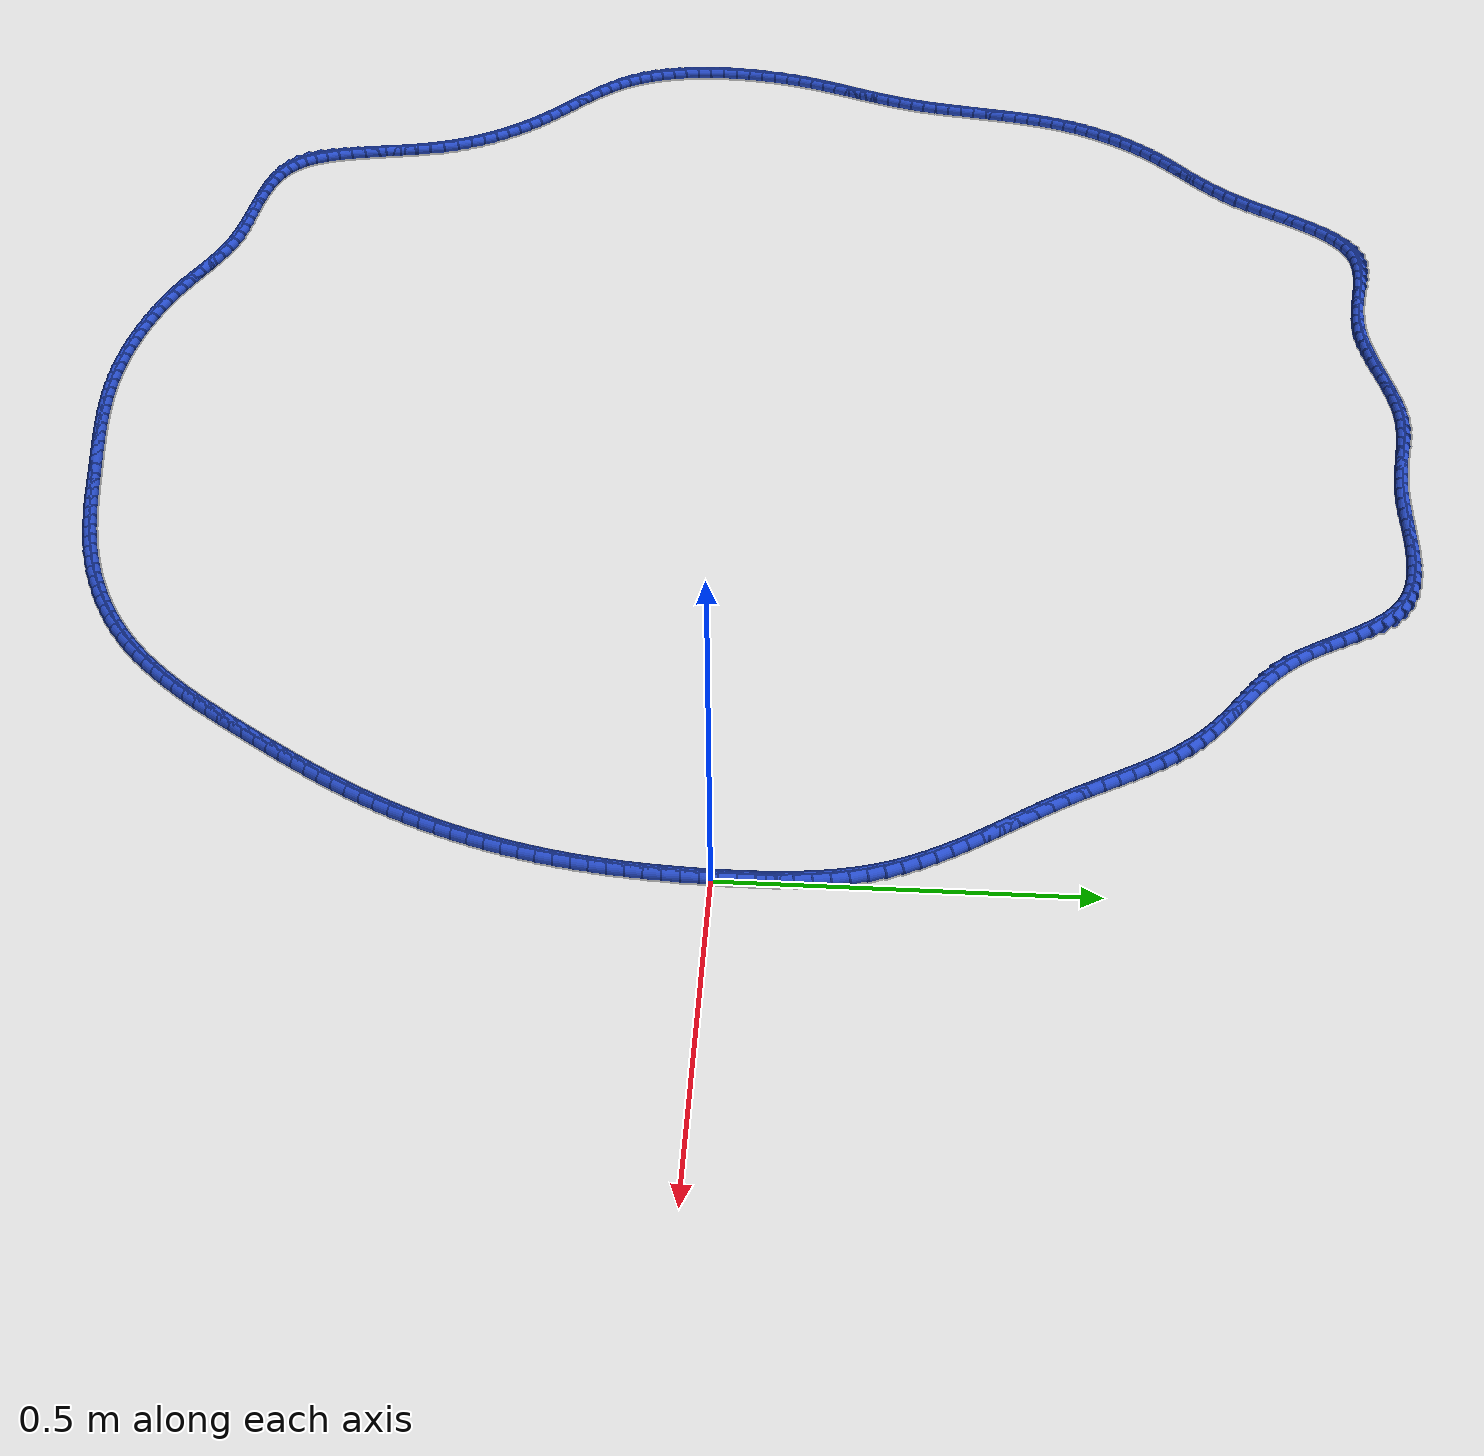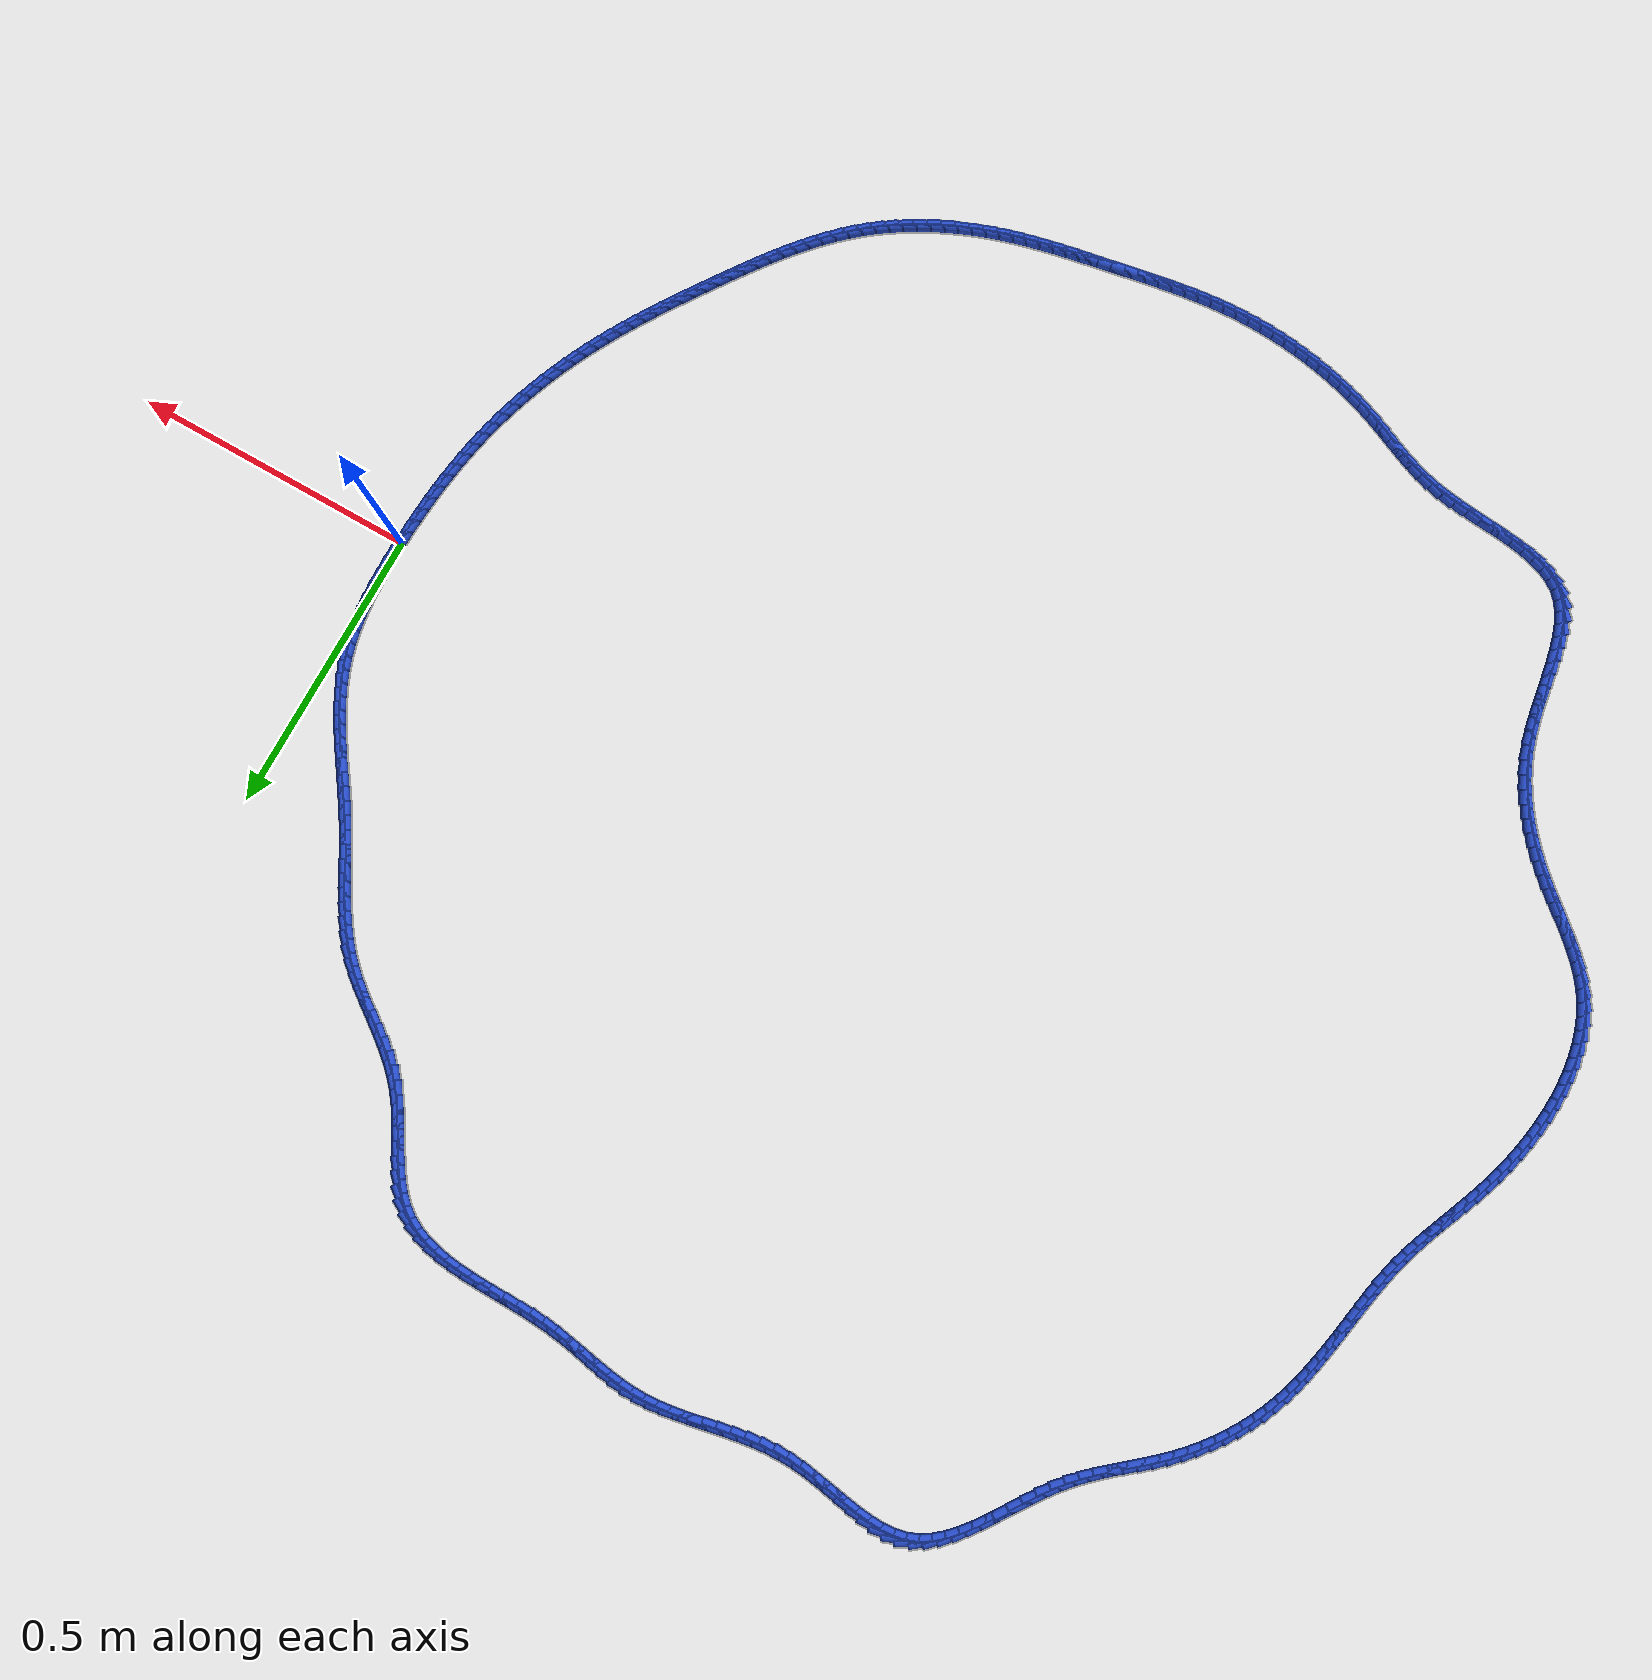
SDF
<sdf version="1.6">
 <world name="default">
  <light name="sun" type="directional">
   <pose>0 0 10 0 -0 0</pose>
   <diffuse>0.8 0.8 0.8 1</diffuse>
   <specular>0.2 0.2 0.2 1</specular>
   <attenuation>
    <range>1000</range>
    <constant>0.9</constant>
    <linear>0.01</linear>
    <quadratic>0.001</quadratic>
   </attenuation>
   <direction>-0.5 0.1 -0.9</direction>
  </light>
  <model name="ground_plane">
   <static>1</static>
   <link name="link">
    <collision name="collision">
     <geometry><plane><normal>0 0 1</normal><size>100 100</size></plane></geometry>
     <surface><friction><ode><mu>100</mu><mu2>50</mu2></ode></friction></surface>
    </collision>
    <visual name="visual">
     <cast_shadows>0</cast_shadows>
     <geometry><plane><normal>0 0 1</normal><size>100 100</size></plane></geometry>
     <material>
      <script><uri>file://media/materials/scripts/gazebo.material</uri><name>Gazebo/WhiteGlow</name></script>
     </material>
    </visual>
   </link>
  </model>
  <gravity>0 0 -9.8</gravity>
  <magnetic_field>6e-06 2.3e-05 -4.2e-05</magnetic_field>
  <atmosphere type="adiabatic"/>
  <physics name="default_physics" default="0" type="ode">
   <max_step_size>0.001</max_step_size>
   <real_time_factor>1</real_time_factor>
   <real_time_update_rate>1000</real_time_update_rate>
  </physics>
  <scene><ambient>0.4 0.4 0.4 1</ambient><background>0.7 0.7 0.7 1</background><shadows>1</shadows></scene>
  <spherical_coordinates>
   <surface_model>EARTH_WGS84</surface_model>
   <latitude_deg>0</latitude_deg>
   <longitude_deg>0</longitude_deg>
   <elevation>0</elevation>
   <heading_deg>0</heading_deg>
  </spherical_coordinates>
  <model name="line">
   <link name="link_0">
    <pose>-5.637851296924623e-18 7.632783294297951e-17 0.01 0 1.57 1.551759685563351</pose>
    <collision name="collision">
     <geometry><cylinder><radius>0.01</radius><length>0.08</length></cylinder></geometry>
    </collision>
    <visual name="visual">
     <material>
      <script><name>Gazebo/Blue</name><uri>file://media/materials/scripts/gazebo.material</uri></script>
     </material>
     <geometry><cylinder><radius>0.01</radius><length>0.08</length></cylinder></geometry>
    </visual>
   </link>
   <link name="link_1">
    <pose>0.0004580631078288707 0.024059274315162388 0.01 0 1.57 1.57023816781488</pose>
    <collision name="collision">
     <geometry><cylinder><radius>0.01</radius><length>0.08</length></cylinder></geometry>
    </collision>
    <visual name="visual">
     <material>
      <script><name>Gazebo/Blue</name><uri>file://media/materials/scripts/gazebo.material</uri></script>
     </material>
     <geometry><cylinder><radius>0.01</radius><length>0.08</length></cylinder></geometry>
    </visual>
   </link>
   <link name="link_2">
    <pose>0.0004715197326204527 0.04816821796012009 0.01 0 1.57 -1.5480966663146645</pose>
    <collision name="collision">
     <geometry><cylinder><radius>0.01</radius><length>0.08</length></cylinder></geometry>
    </collision>
    <visual name="visual">
     <material>
      <script><name>Gazebo/Blue</name><uri>file://media/materials/scripts/gazebo.material</uri></script>
     </material>
     <geometry><cylinder><radius>0.01</radius><length>0.08</length></cylinder></geometry>
    </visual>
   </link>
   <link name="link_3">
    <pose>-7.52854100205284e-05 0.07225277295274624 0.01 0 1.57 -1.5198641492664755</pose>
    <collision name="collision">
     <geometry><cylinder><radius>0.01</radius><length>0.08</length></cylinder></geometry>
    </collision>
    <visual name="visual">
     <material>
      <script><name>Gazebo/Blue</name><uri>file://media/materials/scripts/gazebo.material</uri></script>
     </material>
     <geometry><cylinder><radius>0.01</radius><length>0.08</length></cylinder></geometry>
    </visual>
   </link>
   <link name="link_4">
    <pose>-0.0012980076044893385 0.09623888131091379 0.01 0 1.57 -1.486411320139112</pose>
    <collision name="collision">
     <geometry><cylinder><radius>0.01</radius><length>0.08</length></cylinder></geometry>
    </collision>
    <visual name="visual">
     <material>
      <script><name>Gazebo/Blue</name><uri>file://media/materials/scripts/gazebo.material</uri></script>
     </material>
     <geometry><cylinder><radius>0.01</radius><length>0.08</length></cylinder></geometry>
    </visual>
   </link>
   <link name="link_5">
    <pose>-0.0033123021351812477 0.12005248505249588 0.01 0 1.57 -1.44745912213653</pose>
    <collision name="collision">
     <geometry><cylinder><radius>0.01</radius><length>0.08</length></cylinder></geometry>
    </collision>
    <visual name="visual">
     <material>
      <script><name>Gazebo/Blue</name><uri>file://media/materials/scripts/gazebo.material</uri></script>
     </material>
     <geometry><cylinder><radius>0.01</radius><length>0.08</length></cylinder></geometry>
    </visual>
   </link>
   <link name="link_6">
    <pose>-0.006233824286491522 0.14361952619536547 0.01 0 1.57 -1.4027191875237015</pose>
    <collision name="collision">
     <geometry><cylinder><radius>0.01</radius><length>0.08</length></cylinder></geometry>
    </collision>
    <visual name="visual">
     <material>
      <script><name>Gazebo/Blue</name><uri>file://media/materials/scripts/gazebo.material</uri></script>
     </material>
     <geometry><cylinder><radius>0.01</radius><length>0.08</length></cylinder></geometry>
    </visual>
   </link>
   <link name="link_7">
    <pose>-0.010178229342815426 0.16686594675739563 0.01 0 1.57 -1.351928127336329</pose>
    <collision name="collision">
     <geometry><cylinder><radius>0.01</radius><length>0.08</length></cylinder></geometry>
    </collision>
    <visual name="visual">
     <material>
      <script><name>Gazebo/Blue</name><uri>file://media/materials/scripts/gazebo.material</uri></script>
     </material>
     <geometry><cylinder><radius>0.01</radius><length>0.08</length></cylinder></geometry>
    </visual>
   </link>
   <link name="link_8">
    <pose>-0.015261172588548234 0.18971768875645942 0.01 0 1.57 -1.2948943079299973</pose>
    <collision name="collision">
     <geometry><cylinder><radius>0.01</radius><length>0.08</length></cylinder></geometry>
    </collision>
    <visual name="visual">
     <material>
      <script><name>Gazebo/Blue</name><uri>file://media/materials/scripts/gazebo.material</uri></script>
     </material>
     <geometry><cylinder><radius>0.01</radius><length>0.08</length></cylinder></geometry>
    </visual>
   </link>
   <link name="link_9">
    <pose>-0.021598309308085203 0.21210069421042982 0.01 0 1.57 -1.2318903393593523</pose>
    <collision name="collision">
     <geometry><cylinder><radius>0.01</radius><length>0.08</length></cylinder></geometry>
    </collision>
    <visual name="visual">
     <material>
      <script><name>Gazebo/Blue</name><uri>file://media/materials/scripts/gazebo.material</uri></script>
     </material>
     <geometry><cylinder><radius>0.01</radius><length>0.08</length></cylinder></geometry>
    </visual>
   </link>
   <link name="link_10">
    <pose>-0.02929842534434294 0.23394459547425706 0.01 0 1.57 -1.1699151971321036</pose>
    <collision name="collision">
     <geometry><cylinder><radius>0.01</radius><length>0.08</length></cylinder></geometry>
    </collision>
    <visual name="visual">
     <material>
      <script><name>Gazebo/Blue</name><uri>file://media/materials/scripts/gazebo.material</uri></script>
     </material>
     <geometry><cylinder><radius>0.01</radius><length>0.08</length></cylinder></geometry>
    </visual>
   </link>
   <link name="link_11">
    <pose>-0.03833016874297059 0.25525430841913777 0.01 0 1.57 -1.115789173306907</pose>
    <collision name="collision">
     <geometry><cylinder><radius>0.01</radius><length>0.08</length></cylinder></geometry>
    </collision>
    <visual name="visual">
     <material>
      <script><name>Gazebo/Blue</name><uri>file://media/materials/scripts/gazebo.material</uri></script>
     </material>
     <geometry><cylinder><radius>0.01</radius><length>0.08</length></cylinder></geometry>
    </visual>
   </link>
   <link name="link_12">
    <pose>-0.04853130731297436 0.2761050591724154 0.01 0 1.57 -1.0700203467706122</pose>
    <collision name="collision">
     <geometry><cylinder><radius>0.01</radius><length>0.08</length></cylinder></geometry>
    </collision>
    <visual name="visual">
     <material>
      <script><name>Gazebo/Blue</name><uri>file://media/materials/scripts/gazebo.material</uri></script>
     </material>
     <geometry><cylinder><radius>0.01</radius><length>0.08</length></cylinder></geometry>
    </visual>
   </link>
   <link name="link_13">
    <pose>-0.059734593645443645 0.2965747680898771 0.01 0 1.57 -1.032631912341022</pose>
    <collision name="collision">
     <geometry><cylinder><radius>0.01</radius><length>0.08</length></cylinder></geometry>
    </collision>
    <visual name="visual">
     <material>
      <script><name>Gazebo/Blue</name><uri>file://media/materials/scripts/gazebo.material</uri></script>
     </material>
     <geometry><cylinder><radius>0.01</radius><length>0.08</length></cylinder></geometry>
    </visual>
   </link>
   <link name="link_14">
    <pose>-0.07177278033146778 0.31674135552731036 0.01 0 1.57 -1.0035009921159832</pose>
    <collision name="collision">
     <geometry><cylinder><radius>0.01</radius><length>0.08</length></cylinder></geometry>
    </collision>
    <visual name="visual">
     <material>
      <script><name>Gazebo/Blue</name><uri>file://media/materials/scripts/gazebo.material</uri></script>
     </material>
     <geometry><cylinder><radius>0.01</radius><length>0.08</length></cylinder></geometry>
    </visual>
   </link>
   <link name="link_15">
    <pose>-0.08447861996213626 0.33668274184050284 0.01 0 1.57 -0.9824379393774216</pose>
    <collision name="collision">
     <geometry><cylinder><radius>0.01</radius><length>0.08</length></cylinder></geometry>
    </collision>
    <visual name="visual">
     <material>
      <script><name>Gazebo/Blue</name><uri>file://media/materials/scripts/gazebo.material</uri></script>
     </material>
     <geometry><cylinder><radius>0.01</radius><length>0.08</length></cylinder></geometry>
    </visual>
   </link>
   <link name="link_16">
    <pose>-0.09768486512853843 0.35647684738524177 0.01 0 1.57 -0.9692446579500995</pose>
    <collision name="collision">
     <geometry><cylinder><radius>0.01</radius><length>0.08</length></cylinder></geometry>
    </collision>
    <visual name="visual">
     <material>
      <script><name>Gazebo/Blue</name><uri>file://media/materials/scripts/gazebo.material</uri></script>
     </material>
     <geometry><cylinder><radius>0.01</radius><length>0.08</length></cylinder></geometry>
    </visual>
   </link>
   <link name="link_17">
    <pose>-0.11122426842176367 0.3762015925173147 0.01 0 1.57 -0.9637529402914834</pose>
    <collision name="collision">
     <geometry><cylinder><radius>0.01</radius><length>0.08</length></cylinder></geometry>
    </collision>
    <visual name="visual">
     <material>
      <script><name>Gazebo/Blue</name><uri>file://media/materials/scripts/gazebo.material</uri></script>
     </material>
     <geometry><cylinder><radius>0.01</radius><length>0.08</length></cylinder></geometry>
    </visual>
   </link>
   <link name="link_18">
    <pose>-0.12492958243290138 0.39593489759250905 0.01 0 1.57 -0.9658458031742991</pose>
    <collision name="collision">
     <geometry><cylinder><radius>0.01</radius><length>0.08</length></cylinder></geometry>
    </collision>
    <visual name="visual">
     <material>
      <script><name>Gazebo/Blue</name><uri>file://media/materials/scripts/gazebo.material</uri></script>
     </material>
     <geometry><cylinder><radius>0.01</radius><length>0.08</length></cylinder></geometry>
    </visual>
   </link>
   <link name="link_19">
    <pose>-0.13863355975304098 0.41575468296661233 0.01 0 1.57 -0.9754646992174958</pose>
    <collision name="collision">
     <geometry><cylinder><radius>0.01</radius><length>0.08</length></cylinder></geometry>
    </collision>
    <visual name="visual">
     <material>
      <script><name>Gazebo/Blue</name><uri>file://media/materials/scripts/gazebo.material</uri></script>
     </material>
     <geometry><cylinder><radius>0.01</radius><length>0.08</length></cylinder></geometry>
    </visual>
   </link>
   <link name="link_20">
    <pose>-0.1521689529732719 0.43573886899541203 0.01 0 1.57 -0.9926044126425159</pose>
    <collision name="collision">
     <geometry><cylinder><radius>0.01</radius><length>0.08</length></cylinder></geometry>
    </collision>
    <visual name="visual">
     <material>
      <script><name>Gazebo/Blue</name><uri>file://media/materials/scripts/gazebo.material</uri></script>
     </material>
     <geometry><cylinder><radius>0.01</radius><length>0.08</length></cylinder></geometry>
    </visual>
   </link>
   <link name="link_21">
    <pose>-0.16536851468468344 0.45596537603469545 0.01 0 1.57 -1.0155542861446123</pose>
    <collision name="collision">
     <geometry><cylinder><radius>0.01</radius><length>0.08</length></cylinder></geometry>
    </collision>
    <visual name="visual">
     <material>
      <script><name>Gazebo/Blue</name><uri>file://media/materials/scripts/gazebo.material</uri></script>
     </material>
     <geometry><cylinder><radius>0.01</radius><length>0.08</length></cylinder></geometry>
    </visual>
   </link>
   <link name="link_22">
    <pose>-0.17810003155705945 0.4764887911924175 0.01 0 1.57 -1.0330435236181261</pose>
    <collision name="collision">
     <geometry><cylinder><radius>0.01</radius><length>0.08</length></cylinder></geometry>
    </collision>
    <visual name="visual">
     <material>
      <script><name>Gazebo/Blue</name><uri>file://media/materials/scripts/gazebo.material</uri></script>
     </material>
     <geometry><cylinder><radius>0.01</radius><length>0.08</length></cylinder></geometry>
    </visual>
   </link>
   <link name="link_23">
    <pose>-0.1904589610098408 0.497212069273815 0.01 0 1.57 -1.0405841910014644</pose>
    <collision name="collision">
     <geometry><cylinder><radius>0.01</radius><length>0.08</length></cylinder></geometry>
    </collision>
    <visual name="visual">
     <material>
      <script><name>Gazebo/Blue</name><uri>file://media/materials/scripts/gazebo.material</uri></script>
     </material>
     <geometry><cylinder><radius>0.01</radius><length>0.08</length></cylinder></geometry>
    </visual>
   </link>
   <link name="link_24">
    <pose>-0.20263174001428746 0.5179775712706328 0.01 0 1.57 -1.038127003793174</pose>
    <collision name="collision">
     <geometry><cylinder><radius>0.01</radius><length>0.08</length></cylinder></geometry>
    </collision>
    <visual name="visual">
     <material>
      <script><name>Gazebo/Blue</name><uri>file://media/materials/scripts/gazebo.material</uri></script>
     </material>
     <geometry><cylinder><radius>0.01</radius><length>0.08</length></cylinder></geometry>
    </visual>
   </link>
   <link name="link_25">
    <pose>-0.21480504454830684 0.5386274989924257 0.01 0 1.57 -1.0255348692210922</pose>
    <collision name="collision">
     <geometry><cylinder><radius>0.01</radius><length>0.08</length></cylinder></geometry>
    </collision>
    <visual name="visual">
     <material>
      <script><name>Gazebo/Blue</name><uri>file://media/materials/scripts/gazebo.material</uri></script>
     </material>
     <geometry><cylinder><radius>0.01</radius><length>0.08</length></cylinder></geometry>
    </visual>
   </link>
   <link name="link_26">
    <pose>-0.22716555058980648 0.5590040542487485 0.01 0 1.57 -1.0025745106542154</pose>
    <collision name="collision">
     <geometry><cylinder><radius>0.01</radius><length>0.08</length></cylinder></geometry>
    </collision>
    <visual name="visual">
     <material>
      <script><name>Gazebo/Blue</name><uri>file://media/materials/scripts/gazebo.material</uri></script>
     </material>
     <geometry><cylinder><radius>0.01</radius><length>0.08</length></cylinder></geometry>
    </visual>
   </link>
   <link name="link_27">
    <pose>-0.23989993411669386 0.5789494388491567 0.01 0 1.57 -0.9689510966440771</pose>
    <collision name="collision">
     <geometry><cylinder><radius>0.01</radius><length>0.08</length></cylinder></geometry>
    </collision>
    <visual name="visual">
     <material>
      <script><name>Gazebo/Blue</name><uri>file://media/materials/scripts/gazebo.material</uri></script>
     </material>
     <geometry><cylinder><radius>0.01</radius><length>0.08</length></cylinder></geometry>
    </visual>
   </link>
   <link name="link_28">
    <pose>-0.25319487110687655 0.5983058546032053 0.01 0 1.57 -0.9243808068357932</pose>
    <collision name="collision">
     <geometry><cylinder><radius>0.01</radius><length>0.08</length></cylinder></geometry>
    </collision>
    <visual name="visual">
     <material>
      <script><name>Gazebo/Blue</name><uri>file://media/materials/scripts/gazebo.material</uri></script>
     </material>
     <geometry><cylinder><radius>0.01</radius><length>0.08</length></cylinder></geometry>
    </visual>
   </link>
   <link name="link_29">
    <pose>-0.2672370375382621 0.6169155033204493 0.01 0 1.57 -0.8687090175828311</pose>
    <collision name="collision">
     <geometry><cylinder><radius>0.01</radius><length>0.08</length></cylinder></geometry>
    </collision>
    <visual name="visual">
     <material>
      <script><name>Gazebo/Blue</name><uri>file://media/materials/scripts/gazebo.material</uri></script>
     </material>
     <geometry><cylinder><radius>0.01</radius><length>0.08</length></cylinder></geometry>
    </visual>
   </link>
   <link name="link_30">
    <pose>-0.28221310938875804 0.6346205868104438 0.01 0 1.57 -0.8021210492284885</pose>
    <collision name="collision">
     <geometry><cylinder><radius>0.01</radius><length>0.08</length></cylinder></geometry>
    </collision>
    <visual name="visual">
     <material>
      <script><name>Gazebo/Blue</name><uri>file://media/materials/scripts/gazebo.material</uri></script>
     </material>
     <geometry><cylinder><radius>0.01</radius><length>0.08</length></cylinder></geometry>
    </visual>
   </link>
   <link name="link_31">
    <pose>-0.2983090102558215 0.6512640351183377 0.01 0 1.57 -0.7336708256044858</pose>
    <collision name="collision">
     <geometry><cylinder><radius>0.01</radius><length>0.08</length></cylinder></geometry>
    </collision>
    <visual name="visual">
     <material>
      <script><name>Gazebo/Blue</name><uri>file://media/materials/scripts/gazebo.material</uri></script>
     </material>
     <geometry><cylinder><radius>0.01</radius><length>0.08</length></cylinder></geometry>
    </visual>
   </link>
   <link name="link_32">
    <pose>-0.31556959698871756 0.666825318024033 0.01 0 1.57 -0.6822053867130713</pose>
    <collision name="collision">
     <geometry><cylinder><radius>0.01</radius><length>0.08</length></cylinder></geometry>
    </collision>
    <visual name="visual">
     <material>
      <script><name>Gazebo/Blue</name><uri>file://media/materials/scripts/gazebo.material</uri></script>
     </material>
     <geometry><cylinder><radius>0.01</radius><length>0.08</length></cylinder></geometry>
    </visual>
   </link>
   <link name="link_33">
    <pose>-0.33373359396966285 0.6815802135897588 0.01 0 1.57 -0.6499025332240669</pose>
    <collision name="collision">
     <geometry><cylinder><radius>0.01</radius><length>0.08</length></cylinder></geometry>
    </collision>
    <visual name="visual">
     <material>
      <script><name>Gazebo/Blue</name><uri>file://media/materials/scripts/gazebo.material</uri></script>
     </material>
     <geometry><cylinder><radius>0.01</radius><length>0.08</length></cylinder></geometry>
    </visual>
   </link>
   <link name="link_34">
    <pose>-0.352499605631969 0.6958433323258728 0.01 0 1.57 -0.6362783941563067</pose>
    <collision name="collision">
     <geometry><cylinder><radius>0.01</radius><length>0.08</length></cylinder></geometry>
    </collision>
    <visual name="visual">
     <material>
      <script><name>Gazebo/Blue</name><uri>file://media/materials/scripts/gazebo.material</uri></script>
     </material>
     <geometry><cylinder><radius>0.01</radius><length>0.08</length></cylinder></geometry>
    </visual>
   </link>
   <link name="link_35">
    <pose>-0.37156623640894804 0.709929284742732 0.01 0 1.57 -0.6409452636583325</pose>
    <collision name="collision">
     <geometry><cylinder><radius>0.01</radius><length>0.08</length></cylinder></geometry>
    </collision>
    <visual name="visual">
     <material>
      <script><name>Gazebo/Blue</name><uri>file://media/materials/scripts/gazebo.material</uri></script>
     </material>
     <geometry><cylinder><radius>0.01</radius><length>0.08</length></cylinder></geometry>
    </visual>
   </link>
   <link name="link_36">
    <pose>-0.39063209073391125 0.7241526813506937 0.01 0 1.57 -0.6637430228627839</pose>
    <collision name="collision">
     <geometry><cylinder><radius>0.01</radius><length>0.08</length></cylinder></geometry>
    </collision>
    <visual name="visual">
     <material>
      <script><name>Gazebo/Blue</name><uri>file://media/materials/scripts/gazebo.material</uri></script>
     </material>
     <geometry><cylinder><radius>0.01</radius><length>0.08</length></cylinder></geometry>
    </visual>
   </link>
   <link name="link_37">
    <pose>-0.409395773040171 0.7388281326601155 0.01 0 1.57 -0.7046864514127695</pose>
    <collision name="collision">
     <geometry><cylinder><radius>0.01</radius><length>0.08</length></cylinder></geometry>
    </collision>
    <visual name="visual">
     <material>
      <script><name>Gazebo/Blue</name><uri>file://media/materials/scripts/gazebo.material</uri></script>
     </material>
     <geometry><cylinder><radius>0.01</radius><length>0.08</length></cylinder></geometry>
    </visual>
   </link>
   <link name="link_38">
    <pose>-0.42755588776103853 0.7542702491813543 0.01 0 1.57 -0.7637381152608196</pose>
    <collision name="collision">
     <geometry><cylinder><radius>0.01</radius><length>0.08</length></cylinder></geometry>
    </collision>
    <visual name="visual">
     <material>
      <script><name>Gazebo/Blue</name><uri>file://media/materials/scripts/gazebo.material</uri></script>
     </material>
     <geometry><cylinder><radius>0.01</radius><length>0.08</length></cylinder></geometry>
    </visual>
   </link>
   <link name="link_39">
    <pose>-0.4448110393298259 0.7707936414247677 0.01 0 1.57 -0.8403531457350524</pose>
    <collision name="collision">
     <geometry><cylinder><radius>0.01</radius><length>0.08</length></cylinder></geometry>
    </collision>
    <visual name="visual">
     <material>
      <script><name>Gazebo/Blue</name><uri>file://media/materials/scripts/gazebo.material</uri></script>
     </material>
     <geometry><cylinder><radius>0.01</radius><length>0.08</length></cylinder></geometry>
    </visual>
   </link>
   <link name="link_40">
    <pose>-0.4608606806496912 0.788711867764181 0.01 0 1.57 -0.9210708584065361</pose>
    <collision name="collision">
     <geometry><cylinder><radius>0.01</radius><length>0.08</length></cylinder></geometry>
    </collision>
    <visual name="visual">
     <material>
      <script><name>Gazebo/Blue</name><uri>file://media/materials/scripts/gazebo.material</uri></script>
     </material>
     <geometry><cylinder><radius>0.01</radius><length>0.08</length></cylinder></geometry>
    </visual>
   </link>
   <link name="link_41">
    <pose>-0.4755938269041832 0.8081034217669522 0.01 0 1.57 -0.9785706430964333</pose>
    <collision name="collision">
     <geometry><cylinder><radius>0.01</radius><length>0.08</length></cylinder></geometry>
    </collision>
    <visual name="visual">
     <material>
      <script><name>Gazebo/Blue</name><uri>file://media/materials/scripts/gazebo.material</uri></script>
     </material>
     <geometry><cylinder><radius>0.01</radius><length>0.08</length></cylinder></geometry>
    </visual>
   </link>
   <link name="link_42">
    <pose>-0.4893272907601324 0.8285163110176358 0.01 0 1.57 -1.010795277397516</pose>
    <collision name="collision">
     <geometry><cylinder><radius>0.01</radius><length>0.08</length></cylinder></geometry>
    </collision>
    <visual name="visual">
     <material>
      <script><name>Gazebo/Blue</name><uri>file://media/materials/scripts/gazebo.material</uri></script>
     </material>
     <geometry><cylinder><radius>0.01</radius><length>0.08</length></cylinder></geometry>
    </visual>
   </link>
   <link name="link_43">
    <pose>-0.5024365293088742 0.8494258216697721 0.01 0 1.57 -1.0187813296468595</pose>
    <collision name="collision">
     <geometry><cylinder><radius>0.01</radius><length>0.08</length></cylinder></geometry>
    </collision>
    <visual name="visual">
     <material>
      <script><name>Gazebo/Blue</name><uri>file://media/materials/scripts/gazebo.material</uri></script>
     </material>
     <geometry><cylinder><radius>0.01</radius><length>0.08</length></cylinder></geometry>
    </visual>
   </link>
   <link name="link_44">
    <pose>-0.515296999641744 0.8703072398769003 0.01 0 1.57 -1.0022915188749977</pose>
    <collision name="collision">
     <geometry><cylinder><radius>0.01</radius><length>0.08</length></cylinder></geometry>
    </collision>
    <visual name="visual">
     <material>
      <script><name>Gazebo/Blue</name><uri>file://media/materials/scripts/gazebo.material</uri></script>
     </material>
     <geometry><cylinder><radius>0.01</radius><length>0.08</length></cylinder></geometry>
    </visual>
   </link>
   <link name="link_45">
    <pose>-0.528284158850077 0.8906358517925593 0.01 0 1.57 -0.9595984478614437</pose>
    <collision name="collision">
     <geometry><cylinder><radius>0.01</radius><length>0.08</length></cylinder></geometry>
    </collision>
    <visual name="visual">
     <material>
      <script><name>Gazebo/Blue</name><uri>file://media/materials/scripts/gazebo.material</uri></script>
     </material>
     <geometry><cylinder><radius>0.01</radius><length>0.08</length></cylinder></geometry>
    </visual>
   </link>
   <link name="link_46">
    <pose>-0.5417734640252088 0.9098869435702899 0.01 0 1.57 -0.8875517555663721</pose>
    <collision name="collision">
     <geometry><cylinder><radius>0.01</radius><length>0.08</length></cylinder></geometry>
    </collision>
    <visual name="visual">
     <material>
      <script><name>Gazebo/Blue</name><uri>file://media/materials/scripts/gazebo.material</uri></script>
     </material>
     <geometry><cylinder><radius>0.01</radius><length>0.08</length></cylinder></geometry>
    </visual>
   </link>
   <link name="link_47">
    <pose>-0.5561403722584743 0.9275358013636301 0.01 0 1.57 -0.782249409970126</pose>
    <collision name="collision">
     <geometry><cylinder><radius>0.01</radius><length>0.08</length></cylinder></geometry>
    </collision>
    <visual name="visual">
     <material>
      <script><name>Gazebo/Blue</name><uri>file://media/materials/scripts/gazebo.material</uri></script>
     </material>
     <geometry><cylinder><radius>0.01</radius><length>0.08</length></cylinder></geometry>
    </visual>
   </link>
   <link name="link_48">
    <pose>-0.5717603406412095 0.9430577113261207 0.01 0 1.57 -0.6427934618571559</pose>
    <collision name="collision">
     <geometry><cylinder><radius>0.01</radius><length>0.08</length></cylinder></geometry>
    </collision>
    <visual name="visual">
     <material>
      <script><name>Gazebo/Blue</name><uri>file://media/materials/scripts/gazebo.material</uri></script>
     </material>
     <geometry><cylinder><radius>0.01</radius><length>0.08</length></cylinder></geometry>
    </visual>
   </link>
   <link name="link_49">
    <pose>-0.5889879605136304 0.9559593877809783 0.01 0 1.57 -0.4970556582952676</pose>
    <collision name="collision">
     <geometry><cylinder><radius>0.01</radius><length>0.08</length></cylinder></geometry>
    </collision>
    <visual name="visual">
     <material>
      <script><name>Gazebo/Blue</name><uri>file://media/materials/scripts/gazebo.material</uri></script>
     </material>
     <geometry><cylinder><radius>0.01</radius><length>0.08</length></cylinder></geometry>
    </visual>
   </link>
   <link name="link_50">
    <pose>-0.6078741829763895 0.9662048905318597 0.01 0 1.57 -0.36998339307384254</pose>
    <collision name="collision">
     <geometry><cylinder><radius>0.01</radius><length>0.08</length></cylinder></geometry>
    </collision>
    <visual name="visual">
     <material>
      <script><name>Gazebo/Blue</name><uri>file://media/materials/scripts/gazebo.material</uri></script>
     </material>
     <geometry><cylinder><radius>0.01</radius><length>0.08</length></cylinder></geometry>
    </visual>
   </link>
   <link name="link_51">
    <pose>-0.6282405248722442 0.9741038551896851 0.01 0 1.57 -0.26464778107757725</pose>
    <collision name="collision">
     <geometry><cylinder><radius>0.01</radius><length>0.08</length></cylinder></geometry>
    </collision>
    <visual name="visual">
     <material>
      <script><name>Gazebo/Blue</name><uri>file://media/materials/scripts/gazebo.material</uri></script>
     </material>
     <geometry><cylinder><radius>0.01</radius><length>0.08</length></cylinder></geometry>
    </visual>
   </link>
   <link name="link_52">
    <pose>-0.6499028447881126 0.9799744398778726 0.01 0 1.57 -0.18068676020941668</pose>
    <collision name="collision">
     <geometry><cylinder><radius>0.01</radius><length>0.08</length></cylinder></geometry>
    </collision>
    <visual name="visual">
     <material>
      <script><name>Gazebo/Blue</name><uri>file://media/materials/scripts/gazebo.material</uri></script>
     </material>
     <geometry><cylinder><radius>0.01</radius><length>0.08</length></cylinder></geometry>
    </visual>
   </link>
   <link name="link_53">
    <pose>-0.672677001310911 0.9841348027198382 0.01 0 1.57 -0.11626995606380869</pose>
    <collision name="collision">
     <geometry><cylinder><radius>0.01</radius><length>0.08</length></cylinder></geometry>
    </collision>
    <visual name="visual">
     <material>
      <script><name>Gazebo/Blue</name><uri>file://media/materials/scripts/gazebo.material</uri></script>
     </material>
     <geometry><cylinder><radius>0.01</radius><length>0.08</length></cylinder></geometry>
    </visual>
   </link>
   <link name="link_54">
    <pose>-0.6963788530275564 0.986903101838999 0.01 0 1.57 -0.06920269054851788</pose>
    <collision name="collision">
     <geometry><cylinder><radius>0.01</radius><length>0.08</length></cylinder></geometry>
    </collision>
    <visual name="visual">
     <material>
      <script><name>Gazebo/Blue</name><uri>file://media/materials/scripts/gazebo.material</uri></script>
     </material>
     <geometry><cylinder><radius>0.01</radius><length>0.08</length></cylinder></geometry>
    </visual>
   </link>
   <link name="link_55">
    <pose>-0.7208242585249671 0.9885974953587728 0.01 0 1.57 -0.03752098993456947</pose>
    <collision name="collision">
     <geometry><cylinder><radius>0.01</radius><length>0.08</length></cylinder></geometry>
    </collision>
    <visual name="visual">
     <material>
      <script><name>Gazebo/Blue</name><uri>file://media/materials/scripts/gazebo.material</uri></script>
     </material>
     <geometry><cylinder><radius>0.01</radius><length>0.08</length></cylinder></geometry>
    </visual>
   </link>
   <link name="link_56">
    <pose>-0.745829076390059 0.9895361414025756 0.01 0 1.57 -0.01973955308873256</pose>
    <collision name="collision">
     <geometry><cylinder><radius>0.01</radius><length>0.08</length></cylinder></geometry>
    </collision>
    <visual name="visual">
     <material>
      <script><name>Gazebo/Blue</name><uri>file://media/materials/scripts/gazebo.material</uri></script>
     </material>
     <geometry><cylinder><radius>0.01</radius><length>0.08</length></cylinder></geometry>
    </visual>
   </link>
   <link name="link_57">
    <pose>-0.77120916520975 0.9900371980938252 0.01 0 1.57 -0.014922915592456776</pose>
    <collision name="collision">
     <geometry><cylinder><radius>0.01</radius><length>0.08</length></cylinder></geometry>
    </collision>
    <visual name="visual">
     <material>
      <script><name>Gazebo/Blue</name><uri>file://media/materials/scripts/gazebo.material</uri></script>
     </material>
     <geometry><cylinder><radius>0.01</radius><length>0.08</length></cylinder></geometry>
    </visual>
   </link>
   <link name="link_58">
    <pose>-0.7967803835709568 0.9904188235559381 0.01 0 1.57 -0.0226854372223595</pose>
    <collision name="collision">
     <geometry><cylinder><radius>0.01</radius><length>0.08</length></cylinder></geometry>
    </collision>
    <visual name="visual">
     <material>
      <script><name>Gazebo/Blue</name><uri>file://media/materials/scripts/gazebo.material</uri></script>
     </material>
     <geometry><cylinder><radius>0.01</radius><length>0.08</length></cylinder></geometry>
    </visual>
   </link>
   <link name="link_59">
    <pose>-0.8223585900605968 0.9909991759123314 0.01 0 1.57 -0.04316969333847644</pose>
    <collision name="collision">
     <geometry><cylinder><radius>0.01</radius><length>0.08</length></cylinder></geometry>
    </collision>
    <visual name="visual">
     <material>
      <script><name>Gazebo/Blue</name><uri>file://media/materials/scripts/gazebo.material</uri></script>
     </material>
     <geometry><cylinder><radius>0.01</radius><length>0.08</length></cylinder></geometry>
    </visual>
   </link>
   <link name="link_60">
    <pose>-0.8477596432655872 0.9920964132864226 0.01 0 1.57 -0.07701586255813168</pose>
    <collision name="collision">
     <geometry><cylinder><radius>0.01</radius><length>0.08</length></cylinder></geometry>
    </collision>
    <visual name="visual">
     <material>
      <script><name>Gazebo/Blue</name><uri>file://media/materials/scripts/gazebo.material</uri></script>
     </material>
     <geometry><cylinder><radius>0.01</radius><length>0.08</length></cylinder></geometry>
    </visual>
   </link>
   <link name="link_61">
    <pose>-0.8727994017728447 0.994028693801628 0.01 0 1.57 -0.12044059929523064</pose>
    <collision name="collision">
     <geometry><cylinder><radius>0.01</radius><length>0.08</length></cylinder></geometry>
    </collision>
    <visual name="visual">
     <material>
      <script><name>Gazebo/Blue</name><uri>file://media/materials/scripts/gazebo.material</uri></script>
     </material>
     <geometry><cylinder><radius>0.01</radius><length>0.08</length></cylinder></geometry>
    </visual>
   </link>
   <link name="link_62">
    <pose>-0.897335885524138 0.9969982552724129 0.01 0 1.57 -0.154080676624755</pose>
    <collision name="collision">
     <geometry><cylinder><radius>0.01</radius><length>0.08</length></cylinder></geometry>
    </collision>
    <visual name="visual">
     <material>
      <script><name>Gazebo/Blue</name><uri>file://media/materials/scripts/gazebo.material</uri></script>
     </material>
     <geometry><cylinder><radius>0.01</radius><length>0.08</length></cylinder></geometry>
    </visual>
   </link>
   <link name="link_63">
    <pose>-0.9213987270569008 1.000735496190726 0.01 0 1.57 -0.1721936093367742</pose>
    <collision name="collision">
     <geometry><cylinder><radius>0.01</radius><length>0.08</length></cylinder></geometry>
    </collision>
    <visual name="visual">
     <material>
      <script><name>Gazebo/Blue</name><uri>file://media/materials/scripts/gazebo.material</uri></script>
     </material>
     <geometry><cylinder><radius>0.01</radius><length>0.08</length></cylinder></geometry>
    </visual>
   </link>
   <link name="link_64">
    <pose>-0.9450612168562458 1.0048507799405098 0.01 0 1.57 -0.17407672545674363</pose>
    <collision name="collision">
     <geometry><cylinder><radius>0.01</radius><length>0.08</length></cylinder></geometry>
    </collision>
    <visual name="visual">
     <material>
      <script><name>Gazebo/Blue</name><uri>file://media/materials/scripts/gazebo.material</uri></script>
     </material>
     <geometry><cylinder><radius>0.01</radius><length>0.08</length></cylinder></geometry>
    </visual>
   </link>
   <link name="link_65">
    <pose>-0.9683966454157164 1.0089544698825281 0.01 0 1.57 -0.15905207827372897</pose>
    <collision name="collision">
     <geometry><cylinder><radius>0.01</radius><length>0.08</length></cylinder></geometry>
    </collision>
    <visual name="visual">
     <material>
      <script><name>Gazebo/Blue</name><uri>file://media/materials/scripts/gazebo.material</uri></script>
     </material>
     <geometry><cylinder><radius>0.01</radius><length>0.08</length></cylinder></geometry>
    </visual>
   </link>
   <link name="link_66">
    <pose>-0.9914783032288562 1.0126569293775445 0.01 0 1.57 -0.12645879317815586</pose>
    <collision name="collision">
     <geometry><cylinder><radius>0.01</radius><length>0.08</length></cylinder></geometry>
    </collision>
    <visual name="visual">
     <material>
      <script><name>Gazebo/Blue</name><uri>file://media/materials/scripts/gazebo.material</uri></script>
     </material>
     <geometry><cylinder><radius>0.01</radius><length>0.08</length></cylinder></geometry>
    </visual>
   </link>
   <link name="link_67">
    <pose>-1.014379480789208 1.0155685217863228 0.01 0 1.57 -0.07579946390025402</pose>
    <collision name="collision">
     <geometry><cylinder><radius>0.01</radius><length>0.08</length></cylinder></geometry>
    </collision>
    <visual name="visual">
     <material>
      <script><name>Gazebo/Blue</name><uri>file://media/materials/scripts/gazebo.material</uri></script>
     </material>
     <geometry><cylinder><radius>0.01</radius><length>0.08</length></cylinder></geometry>
    </visual>
   </link>
   <link name="link_68">
    <pose>-1.0371734685903164 1.0172996104696272 0.01 0 1.57 -0.007576227799453368</pose>
    <collision name="collision">
     <geometry><cylinder><radius>0.01</radius><length>0.08</length></cylinder></geometry>
    </collision>
    <visual name="visual">
     <material>
      <script><name>Gazebo/Blue</name><uri>file://media/materials/scripts/gazebo.material</uri></script>
     </material>
     <geometry><cylinder><radius>0.01</radius><length>0.08</length></cylinder></geometry>
    </visual>
   </link>
   <link name="link_69">
    <pose>-1.0599328898154592 1.0174720443286154 0.01 0 1.57 0.06307592778197377</pose>
    <collision name="collision">
     <geometry><cylinder><radius>0.01</radius><length>0.08</length></cylinder></geometry>
    </collision>
    <visual name="visual">
     <material>
      <script><name>Gazebo/Blue</name><uri>file://media/materials/scripts/gazebo.material</uri></script>
     </material>
     <geometry><cylinder><radius>0.01</radius><length>0.08</length></cylinder></geometry>
    </visual>
   </link>
   <link name="link_70">
    <pose>-1.0827114453354116 1.0160333573258074 0.01 0 1.57 0.11936868673856314</pose>
    <collision name="collision">
     <geometry><cylinder><radius>0.01</radius><length>0.08</length></cylinder></geometry>
    </collision>
    <visual name="visual">
     <material>
      <script><name>Gazebo/Blue</name><uri>file://media/materials/scripts/gazebo.material</uri></script>
     </material>
     <geometry><cylinder><radius>0.01</radius><length>0.08</length></cylinder></geometry>
    </visual>
   </link>
   <link name="link_71">
    <pose>-1.1055416852747948 1.0132951236042014 0.01 0 1.57 0.16039445526237603</pose>
    <collision name="collision">
     <geometry><cylinder><radius>0.01</radius><length>0.08</length></cylinder></geometry>
    </collision>
    <visual name="visual">
     <material>
      <script><name>Gazebo/Blue</name><uri>file://media/materials/scripts/gazebo.material</uri></script>
     </material>
     <geometry><cylinder><radius>0.01</radius><length>0.08</length></cylinder></geometry>
    </visual>
   </link>
   <link name="link_72">
    <pose>-1.1284550450287532 1.0095881036899776 0.01 0 1.57 0.18649344169606036</pose>
    <collision name="collision">
     <geometry><cylinder><radius>0.01</radius><length>0.08</length></cylinder></geometry>
    </collision>
    <visual name="visual">
     <material>
      <script><name>Gazebo/Blue</name><uri>file://media/materials/scripts/gazebo.material</uri></script>
     </material>
     <geometry><cylinder><radius>0.01</radius><length>0.08</length></cylinder></geometry>
    </visual>
   </link>
   <link name="link_73">
    <pose>-1.1514829599924317 1.0052430581093152 0.01 0 1.57 0.1981227975161564</pose>
    <collision name="collision">
     <geometry><cylinder><radius>0.01</radius><length>0.08</length></cylinder></geometry>
    </collision>
    <visual name="visual">
     <material>
      <script><name>Gazebo/Blue</name><uri>file://media/materials/scripts/gazebo.material</uri></script>
     </material>
     <geometry><cylinder><radius>0.01</radius><length>0.08</length></cylinder></geometry>
    </visual>
   </link>
   <link name="link_74">
    <pose>-1.1746568655609722 1.0005907473883944 0.01 0 1.57 0.19568815049745364</pose>
    <collision name="collision">
     <geometry><cylinder><radius>0.01</radius><length>0.08</length></cylinder></geometry>
    </collision>
    <visual name="visual">
     <material>
      <script><name>Gazebo/Blue</name><uri>file://media/materials/scripts/gazebo.material</uri></script>
     </material>
     <geometry><cylinder><radius>0.01</radius><length>0.08</length></cylinder></geometry>
    </visual>
   </link>
   <link name="link_75">
    <pose>-1.1980081971295207 0.9959619320533951 0.01 0 1.57 0.1794790953771534</pose>
    <collision name="collision">
     <geometry><cylinder><radius>0.01</radius><length>0.08</length></cylinder></geometry>
    </collision>
    <visual name="visual">
     <material>
      <script><name>Gazebo/Blue</name><uri>file://media/materials/scripts/gazebo.material</uri></script>
     </material>
     <geometry><cylinder><radius>0.01</radius><length>0.08</length></cylinder></geometry>
    </visual>
   </link>
   <link name="link_76">
    <pose>-1.22156839009322 0.9916873726304964 0.01 0 1.57 0.14968988106606124</pose>
    <collision name="collision">
     <geometry><cylinder><radius>0.01</radius><length>0.08</length></cylinder></geometry>
    </collision>
    <visual name="visual">
     <material>
      <script><name>Gazebo/Blue</name><uri>file://media/materials/scripts/gazebo.material</uri></script>
     </material>
     <geometry><cylinder><radius>0.01</radius><length>0.08</length></cylinder></geometry>
    </visual>
   </link>
   <link name="link_77">
    <pose>-1.2453688798472144 0.9880978296458786 0.01 0 1.57 0.10651386305552568</pose>
    <collision name="collision">
     <geometry><cylinder><radius>0.01</radius><length>0.08</length></cylinder></geometry>
    </collision>
    <visual name="visual">
     <material>
      <script><name>Gazebo/Blue</name><uri>file://media/materials/scripts/gazebo.material</uri></script>
     </material>
     <geometry><cylinder><radius>0.01</radius><length>0.08</length></cylinder></geometry>
    </visual>
   </link>
   <link name="link_78">
    <pose>-1.269441101786649 0.9855240636257214 0.01 0 1.57 0.05030455684609905</pose>
    <collision name="collision">
     <geometry><cylinder><radius>0.01</radius><length>0.08</length></cylinder></geometry>
    </collision>
    <visual name="visual">
     <material>
      <script><name>Gazebo/Blue</name><uri>file://media/materials/scripts/gazebo.material</uri></script>
     </material>
     <geometry><cylinder><radius>0.01</radius><length>0.08</length></cylinder></geometry>
    </visual>
   </link>
   <link name="link_79">
    <pose>-1.2938164913066654 0.9842968350962044 0.01 0 1.57 -0.01815058307747033</pose>
    <collision name="collision">
     <geometry><cylinder><radius>0.01</radius><length>0.08</length></cylinder></geometry>
    </collision>
    <visual name="visual">
     <material>
      <script><name>Gazebo/Blue</name><uri>file://media/materials/scripts/gazebo.material</uri></script>
     </material>
     <geometry><cylinder><radius>0.01</radius><length>0.08</length></cylinder></geometry>
    </visual>
   </link>
   <link name="link_80">
    <pose>-1.3185261099796635 0.9847453783404 0.01 0 1.57 -0.08715805834930529</pose>
    <collision name="collision">
     <geometry><cylinder><radius>0.01</radius><length>0.08</length></cylinder></geometry>
    </collision>
    <visual name="visual">
     <material>
      <script><name>Gazebo/Blue</name><uri>file://media/materials/scripts/gazebo.material</uri></script>
     </material>
     <geometry><cylinder><radius>0.01</radius><length>0.08</length></cylinder></geometry>
    </visual>
   </link>
   <link name="link_81">
    <pose>-1.3435353146387479 0.986930668402171 0.01 0 1.57 -0.13483563902305598</pose>
    <collision name="collision">
     <geometry><cylinder><radius>0.01</radius><length>0.08</length></cylinder></geometry>
    </collision>
    <visual name="visual">
     <material>
      <script><name>Gazebo/Blue</name><uri>file://media/materials/scripts/gazebo.material</uri></script>
     </material>
     <geometry><cylinder><radius>0.01</radius><length>0.08</length></cylinder></geometry>
    </visual>
   </link>
   <link name="link_82">
    <pose>-1.3686690180419472 0.99034027540608 0.01 0 1.57 -0.16010407733230406</pose>
    <collision name="collision">
     <geometry><cylinder><radius>0.01</radius><length>0.08</length></cylinder></geometry>
    </collision>
    <visual name="visual">
     <material>
      <script><name>Gazebo/Blue</name><uri>file://media/materials/scripts/gazebo.material</uri></script>
     </material>
     <geometry><cylinder><radius>0.01</radius><length>0.08</length></cylinder></geometry>
    </visual>
   </link>
   <link name="link_83">
    <pose>-1.3937340482133083 0.9943879331441619 0.01 0 1.57 -0.16379808097296114</pose>
    <collision name="collision">
     <geometry><cylinder><radius>0.01</radius><length>0.08</length></cylinder></geometry>
    </collision>
    <visual name="visual">
     <material>
      <script><name>Gazebo/Blue</name><uri>file://media/materials/scripts/gazebo.material</uri></script>
     </material>
     <geometry><cylinder><radius>0.01</radius><length>0.08</length></cylinder></geometry>
    </visual>
   </link>
   <link name="link_84">
    <pose>-1.4185372331768789 0.9984873754084509 0.01 0 1.57 -0.14538295344609778</pose>
    <collision name="collision">
     <geometry><cylinder><radius>0.01</radius><length>0.08</length></cylinder></geometry>
    </collision>
    <visual name="visual">
     <material>
      <script><name>Gazebo/Blue</name><uri>file://media/materials/scripts/gazebo.material</uri></script>
     </material>
     <geometry><cylinder><radius>0.01</radius><length>0.08</length></cylinder></geometry>
    </visual>
   </link>
   <link name="link_85">
    <pose>-1.4428854009567063 1.002052335990982 0.01 0 1.57 -0.10276810762414201</pose>
    <collision name="collision">
     <geometry><cylinder><radius>0.01</radius><length>0.08</length></cylinder></geometry>
    </collision>
    <visual name="visual">
     <material>
      <script><name>Gazebo/Blue</name><uri>file://media/materials/scripts/gazebo.material</uri></script>
     </material>
     <geometry><cylinder><radius>0.01</radius><length>0.08</length></cylinder></geometry>
    </visual>
   </link>
   <link name="link_86">
    <pose>-1.4665853795768375 1.00449654868379 0.01 0 1.57 -0.03223918383461462</pose>
    <collision name="collision">
     <geometry><cylinder><radius>0.01</radius><length>0.08</length></cylinder></geometry>
    </collision>
    <visual name="visual">
     <material>
      <script><name>Gazebo/Blue</name><uri>file://media/materials/scripts/gazebo.material</uri></script>
     </material>
     <geometry><cylinder><radius>0.01</radius><length>0.08</length></cylinder></geometry>
    </visual>
   </link>
   <link name="link_87">
    <pose>-1.4894439970613207 1.0052337472789095 0.01 0 1.57 0.07118066153074996</pose>
    <collision name="collision">
     <geometry><cylinder><radius>0.01</radius><length>0.08</length></cylinder></geometry>
    </collision>
    <visual name="visual">
     <material>
      <script><name>Gazebo/Blue</name><uri>file://media/materials/scripts/gazebo.material</uri></script>
     </material>
     <geometry><cylinder><radius>0.01</radius><length>0.08</length></cylinder></geometry>
    </visual>
   </link>
   <link name="link_88">
    <pose>-1.5112680814342019 1.0036776655683748 0.01 0 1.57 0.21211985672493155</pose>
    <collision name="collision">
     <geometry><cylinder><radius>0.01</radius><length>0.08</length></cylinder></geometry>
    </collision>
    <visual name="visual">
     <material>
      <script><name>Gazebo/Blue</name><uri>file://media/materials/scripts/gazebo.material</uri></script>
     </material>
     <geometry><cylinder><radius>0.01</radius><length>0.08</length></cylinder></geometry>
    </visual>
   </link>
   <link name="link_89">
    <pose>-1.5318644607195286 0.999242037344221 0.01 0 1.57 0.3878888406233534</pose>
    <collision name="collision">
     <geometry><cylinder><radius>0.01</radius><length>0.08</length></cylinder></geometry>
    </collision>
    <visual name="visual">
     <material>
      <script><name>Gazebo/Blue</name><uri>file://media/materials/scripts/gazebo.material</uri></script>
     </material>
     <geometry><cylinder><radius>0.01</radius><length>0.08</length></cylinder></geometry>
    </visual>
   </link>
   <link name="link_90">
    <pose>-1.5510620090791942 0.9913981268513146 0.01 0 1.57 0.5585127356502102</pose>
    <collision name="collision">
     <geometry><cylinder><radius>0.01</radius><length>0.08</length></cylinder></geometry>
    </collision>
    <visual name="visual">
     <material>
      <script><name>Gazebo/Blue</name><uri>file://media/materials/scripts/gazebo.material</uri></script>
     </material>
     <geometry><cylinder><radius>0.01</radius><length>0.08</length></cylinder></geometry>
    </visual>
   </link>
   <link name="link_91">
    <pose>-1.5689263677727396 0.9802350534182234 0.01 0 1.57 0.6970877737793484</pose>
    <collision name="collision">
     <geometry><cylinder><radius>0.01</radius><length>0.08</length></cylinder></geometry>
    </collision>
    <visual name="visual">
     <material>
      <script><name>Gazebo/Blue</name><uri>file://media/materials/scripts/gazebo.material</uri></script>
     </material>
     <geometry><cylinder><radius>0.01</radius><length>0.08</length></cylinder></geometry>
    </visual>
   </link>
   <link name="link_92">
    <pose>-1.5856671459478928 0.96621762747456 0.01 0 1.57 0.8031688857201666</pose>
    <collision name="collision">
     <geometry><cylinder><radius>0.01</radius><length>0.08</length></cylinder></geometry>
    </collision>
    <visual name="visual">
     <material>
      <script><name>Gazebo/Blue</name><uri>file://media/materials/scripts/gazebo.material</uri></script>
     </material>
     <geometry><cylinder><radius>0.01</radius><length>0.08</length></cylinder></geometry>
    </visual>
   </link>
   <link name="link_93">
    <pose>-1.6014959867010399 0.9498159671363919 0.01 0 1.57 0.880410808872035</pose>
    <collision name="collision">
     <geometry><cylinder><radius>0.01</radius><length>0.08</length></cylinder></geometry>
    </collision>
    <visual name="visual">
     <material>
      <script><name>Gazebo/Blue</name><uri>file://media/materials/scripts/gazebo.material</uri></script>
     </material>
     <geometry><cylinder><radius>0.01</radius><length>0.08</length></cylinder></geometry>
    </visual>
   </link>
   <link name="link_94">
    <pose>-1.6166245331285674 0.9315001905197868 0.01 0 1.57 0.9331486860984257</pose>
    <collision name="collision">
     <geometry><cylinder><radius>0.01</radius><length>0.08</length></cylinder></geometry>
    </collision>
    <visual name="visual">
     <material>
      <script><name>Gazebo/Blue</name><uri>file://media/materials/scripts/gazebo.material</uri></script>
     </material>
     <geometry><cylinder><radius>0.01</radius><length>0.08</length></cylinder></geometry>
    </visual>
   </link>
   <link name="link_95">
    <pose>-1.6312644283268596 0.911740415740811 0.01 0 1.57 0.9649642072845664</pose>
    <collision name="collision">
     <geometry><cylinder><radius>0.01</radius><length>0.08</length></cylinder></geometry>
    </collision>
    <visual name="visual">
     <material>
      <script><name>Gazebo/Blue</name><uri>file://media/materials/scripts/gazebo.material</uri></script>
     </material>
     <geometry><cylinder><radius>0.01</radius><length>0.08</length></cylinder></geometry>
    </visual>
   </link>
   <link name="link_96">
    <pose>-1.6456273153923022 0.891006760915533 0.01 0 1.57 0.9782682983899156</pose>
    <collision name="collision">
     <geometry><cylinder><radius>0.01</radius><length>0.08</length></cylinder></geometry>
    </collision>
    <visual name="visual">
     <material>
      <script><name>Gazebo/Blue</name><uri>file://media/materials/scripts/gazebo.material</uri></script>
     </material>
     <geometry><cylinder><radius>0.01</radius><length>0.08</length></cylinder></geometry>
    </visual>
   </link>
   <link name="link_97">
    <pose>-1.6599248374212805 0.8697693441600195 0.01 0 1.57 0.9742796628503599</pose>
    <collision name="collision">
     <geometry><cylinder><radius>0.01</radius><length>0.08</length></cylinder></geometry>
    </collision>
    <visual name="visual">
     <material>
      <script><name>Gazebo/Blue</name><uri>file://media/materials/scripts/gazebo.material</uri></script>
     </material>
     <geometry><cylinder><radius>0.01</radius><length>0.08</length></cylinder></geometry>
    </visual>
   </link>
   <link name="link_98">
    <pose>-1.6743686375101796 0.8484982835903376 0.01 0 1.57 0.9530980329613442</pose>
    <collision name="collision">
     <geometry><cylinder><radius>0.01</radius><length>0.08</length></cylinder></geometry>
    </collision>
    <visual name="visual">
     <material>
      <script><name>Gazebo/Blue</name><uri>file://media/materials/scripts/gazebo.material</uri></script>
     </material>
     <geometry><cylinder><radius>0.01</radius><length>0.08</length></cylinder></geometry>
    </visual>
   </link>
   <link name="link_99">
    <pose>-1.6891703587553855 0.8276636973225554 0.01 0 1.57 0.9137760798677704</pose>
    <collision name="collision">
     <geometry><cylinder><radius>0.01</radius><length>0.08</length></cylinder></geometry>
    </collision>
    <visual name="visual">
     <material>
      <script><name>Gazebo/Blue</name><uri>file://media/materials/scripts/gazebo.material</uri></script>
     </material>
     <geometry><cylinder><radius>0.01</radius><length>0.08</length></cylinder></geometry>
    </visual>
   </link>
   <link name="link_100">
    <pose>-1.7045416442532844 0.8077357034727393 0.01 0 1.57 0.8559955010344802</pose>
    <collision name="collision">
     <geometry><cylinder><radius>0.01</radius><length>0.08</length></cylinder></geometry>
    </collision>
    <visual name="visual">
     <material>
      <script><name>Gazebo/Blue</name><uri>file://media/materials/scripts/gazebo.material</uri></script>
     </material>
     <geometry><cylinder><radius>0.01</radius><length>0.08</length></cylinder></geometry>
    </visual>
   </link>
   <link name="link_101">
    <pose>-1.7206748144702826 0.7891471946806231 0.01 0 1.57 0.7975324860518057</pose>
    <collision name="collision">
     <geometry><cylinder><radius>0.01</radius><length>0.08</length></cylinder></geometry>
    </collision>
    <visual name="visual">
     <material>
      <script><name>Gazebo/Blue</name><uri>file://media/materials/scripts/gazebo.material</uri></script>
     </material>
     <geometry><cylinder><radius>0.01</radius><length>0.08</length></cylinder></geometry>
    </visual>
   </link>
   <link name="link_102">
    <pose>-1.737528023401738 0.7718799366722274 0.01 0 1.57 0.7523718968551583</pose>
    <collision name="collision">
     <geometry><cylinder><radius>0.01</radius><length>0.08</length></cylinder></geometry>
    </collision>
    <visual name="visual">
     <material>
      <script><name>Gazebo/Blue</name><uri>file://media/materials/scripts/gazebo.material</uri></script>
     </material>
     <geometry><cylinder><radius>0.01</radius><length>0.08</length></cylinder></geometry>
    </visual>
   </link>
   <link name="link_103">
    <pose>-1.7549036925361503 0.7556156730360405 0.01 0 1.57 0.7220029866958872</pose>
    <collision name="collision">
     <geometry><cylinder><radius>0.01</radius><length>0.08</length></cylinder></geometry>
    </collision>
    <visual name="visual">
     <material>
      <script><name>Gazebo/Blue</name><uri>file://media/materials/scripts/gazebo.material</uri></script>
     </material>
     <geometry><cylinder><radius>0.01</radius><length>0.08</length></cylinder></geometry>
    </visual>
   </link>
   <link name="link_104">
    <pose>-1.772601430320051 0.7400307279726472 0.01 0 1.57 0.7071854755017511</pose>
    <collision name="collision">
     <geometry><cylinder><radius>0.01</radius><length>0.08</length></cylinder></geometry>
    </collision>
    <visual name="visual">
     <material>
      <script><name>Gazebo/Blue</name><uri>file://media/materials/scripts/gazebo.material</uri></script>
     </material>
     <geometry><cylinder><radius>0.01</radius><length>0.08</length></cylinder></geometry>
    </visual>
   </link>
   <link name="link_105">
    <pose>-1.7904208451999728 0.724801425682633 0.01 0 1.57 0.7083344225783952</pose>
    <collision name="collision">
     <geometry><cylinder><radius>0.01</radius><length>0.08</length></cylinder></geometry>
    </collision>
    <visual name="visual">
     <material>
      <script><name>Gazebo/Blue</name><uri>file://media/materials/scripts/gazebo.material</uri></script>
     </material>
     <geometry><cylinder><radius>0.01</radius><length>0.08</length></cylinder></geometry>
    </visual>
   </link>
   <link name="link_106">
    <pose>-1.808161545622449 0.7096040903665838 0.01 0 1.57 0.7256057258436636</pose>
    <collision name="collision">
     <geometry><cylinder><radius>0.01</radius><length>0.08</length></cylinder></geometry>
    </collision>
    <visual name="visual">
     <material>
      <script><name>Gazebo/Blue</name><uri>file://media/materials/scripts/gazebo.material</uri></script>
     </material>
     <geometry><cylinder><radius>0.01</radius><length>0.08</length></cylinder></geometry>
    </visual>
   </link>
   <link name="link_107">
    <pose>-1.8256231400340117 0.6941150462250842 0.01 0 1.57 0.758877932166949</pose>
    <collision name="collision">
     <geometry><cylinder><radius>0.01</radius><length>0.08</length></cylinder></geometry>
    </collision>
    <visual name="visual">
     <material>
      <script><name>Gazebo/Blue</name><uri>file://media/materials/scripts/gazebo.material</uri></script>
     </material>
     <geometry><cylinder><radius>0.01</radius><length>0.08</length></cylinder></geometry>
    </visual>
   </link>
   <link name="link_108">
    <pose>-1.842605236881194 0.6780106174587198 0.01 0 1.57 0.8057961049189927</pose>
    <collision name="collision">
     <geometry><cylinder><radius>0.01</radius><length>0.08</length></cylinder></geometry>
    </collision>
    <visual name="visual">
     <material>
      <script><name>Gazebo/Blue</name><uri>file://media/materials/scripts/gazebo.material</uri></script>
     </material>
     <geometry><cylinder><radius>0.01</radius><length>0.08</length></cylinder></geometry>
    </visual>
   </link>
   <link name="link_109">
    <pose>-1.858921699658098 0.6610145534506484 0.01 0 1.57 0.8559095049342595</pose>
    <collision name="collision">
     <geometry><cylinder><radius>0.01</radius><length>0.08</length></cylinder></geometry>
    </collision>
    <visual name="visual">
     <material>
      <script><name>Gazebo/Blue</name><uri>file://media/materials/scripts/gazebo.material</uri></script>
     </material>
     <geometry><cylinder><radius>0.01</radius><length>0.08</length></cylinder></geometry>
    </visual>
   </link>
   <link name="link_110">
    <pose>-1.8744642572833088 0.6431096544187846 0.01 0 1.57 0.9061396930807545</pose>
    <collision name="collision">
     <geometry><cylinder><radius>0.01</radius><length>0.08</length></cylinder></geometry>
    </collision>
    <visual name="visual">
     <material>
      <script><name>Gazebo/Blue</name><uri>file://media/materials/scripts/gazebo.material</uri></script>
     </material>
     <geometry><cylinder><radius>0.01</radius><length>0.08</length></cylinder></geometry>
    </visual>
   </link>
   <link name="link_111">
    <pose>-1.889151092295235 0.6243667292491083 0.01 0 1.57 0.9569034292529092</pose>
    <collision name="collision">
     <geometry><cylinder><radius>0.01</radius><length>0.08</length></cylinder></geometry>
    </collision>
    <visual name="visual">
     <material>
      <script><name>Gazebo/Blue</name><uri>file://media/materials/scripts/gazebo.material</uri></script>
     </material>
     <geometry><cylinder><radius>0.01</radius><length>0.08</length></cylinder></geometry>
    </visual>
   </link>
   <link name="link_112">
    <pose>-1.9029004089729453 0.6048566591566995 0.01 0 1.57 1.008609146119506</pose>
    <collision name="collision">
     <geometry><cylinder><radius>0.01</radius><length>0.08</length></cylinder></geometry>
    </collision>
    <visual name="visual">
     <material>
      <script><name>Gazebo/Blue</name><uri>file://media/materials/scripts/gazebo.material</uri></script>
     </material>
     <geometry><cylinder><radius>0.01</radius><length>0.08</length></cylinder></geometry>
    </visual>
   </link>
   <link name="link_113">
    <pose>-1.9156304115955083 0.584650325356638 0.01 0 1.57 1.0616563224209234</pose>
    <collision name="collision">
     <geometry><cylinder><radius>0.01</radius><length>0.08</length></cylinder></geometry>
    </collision>
    <visual name="visual">
     <material>
      <script><name>Gazebo/Blue</name><uri>file://media/materials/scripts/gazebo.material</uri></script>
     </material>
     <geometry><cylinder><radius>0.01</radius><length>0.08</length></cylinder></geometry>
    </visual>
   </link>
   <link name="link_114">
    <pose>-1.92725930444199 0.5638186090640037 0.01 0 1.57 1.1164355143466824</pose>
    <collision name="collision">
     <geometry><cylinder><radius>0.01</radius><length>0.08</length></cylinder></geometry>
    </collision>
    <visual name="visual">
     <material>
      <script><name>Gazebo/Blue</name><uri>file://media/materials/scripts/gazebo.material</uri></script>
     </material>
     <geometry><cylinder><radius>0.01</radius><length>0.08</length></cylinder></geometry>
    </visual>
   </link>
   <link name="link_115">
    <pose>-1.9377052917914606 0.5424323914938775 0.01 0 1.57 1.1732301114542298</pose>
    <collision name="collision">
     <geometry><cylinder><radius>0.01</radius><length>0.08</length></cylinder></geometry>
    </collision>
    <visual name="visual">
     <material>
      <script><name>Gazebo/Blue</name><uri>file://media/materials/scripts/gazebo.material</uri></script>
     </material>
     <geometry><cylinder><radius>0.01</radius><length>0.08</length></cylinder></geometry>
    </visual>
   </link>
   <link name="link_116">
    <pose>-1.9468890710955187 0.5205624661918841 0.01 0 1.57 1.2283323541265865</pose>
    <collision name="collision">
     <geometry><cylinder><radius>0.01</radius><length>0.08</length></cylinder></geometry>
    </collision>
    <visual name="visual">
     <material>
      <script><name>Gazebo/Blue</name><uri>file://media/materials/scripts/gazebo.material</uri></script>
     </material>
     <geometry><cylinder><radius>0.01</radius><length>0.08</length></cylinder></geometry>
    </visual>
   </link>
   <link name="link_117">
    <pose>-1.9548344543313327 0.49827600080368467 0.01 0 1.57 1.276252975897163</pose>
    <collision name="collision">
     <geometry><cylinder><radius>0.01</radius><length>0.08</length></cylinder></geometry>
    </collision>
    <visual name="visual">
     <material>
      <script><name>Gazebo/Blue</name><uri>file://media/materials/scripts/gazebo.material</uri></script>
     </material>
     <geometry><cylinder><radius>0.01</radius><length>0.08</length></cylinder></geometry>
    </visual>
   </link>
   <link name="link_118">
    <pose>-1.9617028996546562 0.47563532281036447 0.01 0 1.57 1.3164285867788437</pose>
    <collision name="collision">
     <geometry><cylinder><radius>0.01</radius><length>0.08</length></cylinder></geometry>
    </collision>
    <visual name="visual">
     <material>
      <script><name>Gazebo/Blue</name><uri>file://media/materials/scripts/gazebo.material</uri></script>
     </material>
     <geometry><cylinder><radius>0.01</radius><length>0.08</length></cylinder></geometry>
    </visual>
   </link>
   <link name="link_119">
    <pose>-1.9676654458582215 0.45270242280127415 0.01 0 1.57 1.348825281284382</pose>
    <collision name="collision">
     <geometry><cylinder><radius>0.01</radius><length>0.08</length></cylinder></geometry>
    </collision>
    <visual name="visual">
     <material>
      <script><name>Gazebo/Blue</name><uri>file://media/materials/scripts/gazebo.material</uri></script>
     </material>
     <geometry><cylinder><radius>0.01</radius><length>0.08</length></cylinder></geometry>
    </visual>
   </link>
   <link name="link_120">
    <pose>-1.97289313173476 0.4295392913657644 0.01 0 1.57 1.3735000950792597</pose>
    <collision name="collision">
     <geometry><cylinder><radius>0.01</radius><length>0.08</length></cylinder></geometry>
    </collision>
    <visual name="visual">
     <material>
      <script><name>Gazebo/Blue</name><uri>file://media/materials/scripts/gazebo.material</uri></script>
     </material>
     <geometry><cylinder><radius>0.01</radius><length>0.08</length></cylinder></geometry>
    </visual>
   </link>
   <link name="link_121">
    <pose>-1.9775569960770019 0.40620791909318604 0.01 0 1.57 1.3905424134326463</pose>
    <collision name="collision">
     <geometry><cylinder><radius>0.01</radius><length>0.08</length></cylinder></geometry>
    </collision>
    <visual name="visual">
     <material>
      <script><name>Gazebo/Blue</name><uri>file://media/materials/scripts/gazebo.material</uri></script>
     </material>
     <geometry><cylinder><radius>0.01</radius><length>0.08</length></cylinder></geometry>
    </visual>
   </link>
   <link name="link_122">
    <pose>-1.9818280776776798 0.3827702965728898 0.01 0 1.57 1.4000306242163725</pose>
    <collision name="collision">
     <geometry><cylinder><radius>0.01</radius><length>0.08</length></cylinder></geometry>
    </collision>
    <visual name="visual">
     <material>
      <script><name>Gazebo/Blue</name><uri>file://media/materials/scripts/gazebo.material</uri></script>
     </material>
     <geometry><cylinder><radius>0.01</radius><length>0.08</length></cylinder></geometry>
    </visual>
   </link>
   <link name="link_123">
    <pose>-1.9858774153295247 0.3592884143942272 0.01 0 1.57 1.4020033028549446</pose>
    <collision name="collision">
     <geometry><cylinder><radius>0.01</radius><length>0.08</length></cylinder></geometry>
    </collision>
    <visual name="visual">
     <material>
      <script><name>Gazebo/Blue</name><uri>file://media/materials/scripts/gazebo.material</uri></script>
     </material>
     <geometry><cylinder><radius>0.01</radius><length>0.08</length></cylinder></geometry>
    </visual>
   </link>
   <link name="link_124">
    <pose>-1.9898760478252684 0.33582426314654873 0.01 0 1.57 1.3964433944768775</pose>
    <collision name="collision">
     <geometry><cylinder><radius>0.01</radius><length>0.08</length></cylinder></geometry>
    </collision>
    <visual name="visual">
     <material>
      <script><name>Gazebo/Blue</name><uri>file://media/materials/scripts/gazebo.material</uri></script>
     </material>
     <geometry><cylinder><radius>0.01</radius><length>0.08</length></cylinder></geometry>
    </visual>
   </link>
   <link name="link_125">
    <pose>-1.9939950139576414 0.31243983341920517 0.01 0 1.57 1.383274314745042</pose>
    <collision name="collision">
     <geometry><cylinder><radius>0.01</radius><length>0.08</length></cylinder></geometry>
    </collision>
    <visual name="visual">
     <material>
      <script><name>Gazebo/Blue</name><uri>file://media/materials/scripts/gazebo.material</uri></script>
     </material>
     <geometry><cylinder><radius>0.01</radius><length>0.08</length></cylinder></geometry>
    </visual>
   </link>
   <link name="link_126">
    <pose>-1.9984053525193768 0.2891971158015473 0.01 0 1.57 1.362368000612903</pose>
    <collision name="collision">
     <geometry><cylinder><radius>0.01</radius><length>0.08</length></cylinder></geometry>
    </collision>
    <visual name="visual">
     <material>
      <script><name>Gazebo/Blue</name><uri>file://media/materials/scripts/gazebo.material</uri></script>
     </material>
     <geometry><cylinder><radius>0.01</radius><length>0.08</length></cylinder></geometry>
    </visual>
   </link>
   <link name="link_127">
    <pose>-2.003278102303205 0.2661581008829264 0.01 0 1.57 1.3335662292514299</pose>
    <collision name="collision">
     <geometry><cylinder><radius>0.01</radius><length>0.08</length></cylinder></geometry>
    </collision>
    <visual name="visual">
     <material>
      <script><name>Gazebo/Blue</name><uri>file://media/materials/scripts/gazebo.material</uri></script>
     </material>
     <geometry><cylinder><radius>0.01</radius><length>0.08</length></cylinder></geometry>
    </visual>
   </link>
   <link name="link_128">
    <pose>-2.0087843021018568 0.2433847792526932 0.01 0 1.57 1.296734650177814</pose>
    <collision name="collision">
     <geometry><cylinder><radius>0.01</radius><length>0.08</length></cylinder></geometry>
    </collision>
    <visual name="visual">
     <material>
      <script><name>Gazebo/Blue</name><uri>file://media/materials/scripts/gazebo.material</uri></script>
     </material>
     <geometry><cylinder><radius>0.01</radius><length>0.08</length></cylinder></geometry>
    </visual>
   </link>
   <link name="link_129">
    <pose>-2.0150946253811908 0.22093896520659895 0.01 0 1.57 1.2565068963530583</pose>
    <collision name="collision">
     <geometry><cylinder><radius>0.01</radius><length>0.08</length></cylinder></geometry>
    </collision>
    <visual name="visual">
     <material>
      <script><name>Gazebo/Blue</name><uri>file://media/materials/scripts/gazebo.material</uri></script>
     </material>
     <geometry><cylinder><radius>0.01</radius><length>0.08</length></cylinder></geometry>
    </visual>
   </link>
   <link name="link_130">
    <pose>-2.022280030105371 0.19883435392842608 0.01 0 1.57 1.2241785798979505</pose>
    <collision name="collision">
     <geometry><cylinder><radius>0.01</radius><length>0.08</length></cylinder></geometry>
    </collision>
    <visual name="visual">
     <material>
      <script><name>Gazebo/Blue</name><uri>file://media/materials/scripts/gazebo.material</uri></script>
     </material>
     <geometry><cylinder><radius>0.01</radius><length>0.08</length></cylinder></geometry>
    </visual>
   </link>
   <link name="link_131">
    <pose>-2.0301769166240673 0.17697145153984434 0.01 0 1.57 1.201591980708671</pose>
    <collision name="collision">
     <geometry><cylinder><radius>0.01</radius><length>0.08</length></cylinder></geometry>
    </collision>
    <visual name="visual">
     <material>
      <script><name>Gazebo/Blue</name><uri>file://media/materials/scripts/gazebo.material</uri></script>
     </material>
     <geometry><cylinder><radius>0.01</radius><length>0.08</length></cylinder></geometry>
    </visual>
   </link>
   <link name="link_132">
    <pose>-2.03858798749009 0.1552345028186745 0.01 0 1.57 1.1888125237527398</pose>
    <collision name="collision">
     <geometry><cylinder><radius>0.01</radius><length>0.08</length></cylinder></geometry>
    </collision>
    <visual name="visual">
     <material>
      <script><name>Gazebo/Blue</name><uri>file://media/materials/scripts/gazebo.material</uri></script>
     </material>
     <geometry><cylinder><radius>0.01</radius><length>0.08</length></cylinder></geometry>
    </visual>
   </link>
   <link name="link_133">
    <pose>-2.0473159452562486 0.13350775254273622 0.01 0 1.57 1.1857721086222544</pose>
    <collision name="collision">
     <geometry><cylinder><radius>0.01</radius><length>0.08</length></cylinder></geometry>
    </collision>
    <visual name="visual">
     <material>
      <script><name>Gazebo/Blue</name><uri>file://media/materials/scripts/gazebo.material</uri></script>
     </material>
     <geometry><cylinder><radius>0.01</radius><length>0.08</length></cylinder></geometry>
    </visual>
   </link>
   <link name="link_134">
    <pose>-2.056163492475354 0.11167544548984963 0.01 0 1.57 1.192308931952606</pose>
    <collision name="collision">
     <geometry><cylinder><radius>0.01</radius><length>0.08</length></cylinder></geometry>
    </collision>
    <visual name="visual">
     <material>
      <script><name>Gazebo/Blue</name><uri>file://media/materials/scripts/gazebo.material</uri></script>
     </material>
     <geometry><cylinder><radius>0.01</radius><length>0.08</length></cylinder></geometry>
    </visual>
   </link>
   <link name="link_135">
    <pose>-2.064933331700217 0.08962182643783434 0.01 0 1.57 1.2081812324749797</pose>
    <collision name="collision">
     <geometry><cylinder><radius>0.01</radius><length>0.08</length></cylinder></geometry>
    </collision>
    <visual name="visual">
     <material>
      <script><name>Gazebo/Blue</name><uri>file://media/materials/scripts/gazebo.material</uri></script>
     </material>
     <geometry><cylinder><radius>0.01</radius><length>0.08</length></cylinder></geometry>
    </visual>
   </link>
   <link name="link_136">
    <pose>-2.073428165483647 0.06723114016451112 0.01 0 1.57 1.2330571273184296</pose>
    <collision name="collision">
     <geometry><cylinder><radius>0.01</radius><length>0.08</length></cylinder></geometry>
    </collision>
    <visual name="visual">
     <material>
      <script><name>Gazebo/Blue</name><uri>file://media/materials/scripts/gazebo.material</uri></script>
     </material>
     <geometry><cylinder><radius>0.01</radius><length>0.08</length></cylinder></geometry>
    </visual>
   </link>
   <link name="link_137">
    <pose>-2.0814506963784534 0.04438763144769965 0.01 0 1.57 1.2664457687484791</pose>
    <collision name="collision">
     <geometry><cylinder><radius>0.01</radius><length>0.08</length></cylinder></geometry>
    </collision>
    <visual name="visual">
     <material>
      <script><name>Gazebo/Blue</name><uri>file://media/materials/scripts/gazebo.material</uri></script>
     </material>
     <geometry><cylinder><radius>0.01</radius><length>0.08</length></cylinder></geometry>
    </visual>
   </link>
   <link name="link_138">
    <pose>-2.088804234842382 0.020976887687902342 0.01 0 1.57 1.3052134021841537</pose>
    <collision name="collision">
     <geometry><cylinder><radius>0.01</radius><length>0.08</length></cylinder></geometry>
    </collision>
    <visual name="visual">
     <material>
      <script><name>Gazebo/Blue</name><uri>file://media/materials/scripts/gazebo.material</uri></script>
     </material>
     <geometry><cylinder><radius>0.01</radius><length>0.08</length></cylinder></geometry>
    </visual>
   </link>
   <link name="link_139">
    <pose>-2.095332996278438 -0.003025160793633577 0.01 0 1.57 1.3452769497337542</pose>
    <collision name="collision">
     <geometry><cylinder><radius>0.01</radius><length>0.08</length></cylinder></geometry>
    </collision>
    <visual name="visual">
     <material>
      <script><name>Gazebo/Blue</name><uri>file://media/materials/scripts/gazebo.material</uri></script>
     </material>
     <geometry><cylinder><radius>0.01</radius><length>0.08</length></cylinder></geometry>
    </visual>
   </link>
   <link name="link_140">
    <pose>-2.100947286793525 -0.02749661532915055 0.01 0 1.57 1.386808997985382</pose>
    <collision name="collision">
     <geometry><cylinder><radius>0.01</radius><length>0.08</length></cylinder></geometry>
    </collision>
    <visual name="visual">
     <material>
      <script><name>Gazebo/Blue</name><uri>file://media/materials/scripts/gazebo.material</uri></script>
     </material>
     <geometry><cylinder><radius>0.01</radius><length>0.08</length></cylinder></geometry>
    </visual>
   </link>
   <link name="link_141">
    <pose>-2.105563423923904 -0.052302300369996446 0.01 0 1.57 1.4303812375989882</pose>
    <collision name="collision">
     <geometry><cylinder><radius>0.01</radius><length>0.08</length></cylinder></geometry>
    </collision>
    <visual name="visual">
     <material>
      <script><name>Gazebo/Blue</name><uri>file://media/materials/scripts/gazebo.material</uri></script>
     </material>
     <geometry><cylinder><radius>0.01</radius><length>0.08</length></cylinder></geometry>
    </visual>
   </link>
   <link name="link_142">
    <pose>-2.1090977252058356 -0.07730704036752022 0.01 0 1.57 1.476584101286767</pose>
    <collision name="collision">
     <geometry><cylinder><radius>0.01</radius><length>0.08</length></cylinder></geometry>
    </collision>
    <visual name="visual">
     <material>
      <script><name>Gazebo/Blue</name><uri>file://media/materials/scripts/gazebo.material</uri></script>
     </material>
     <geometry><cylinder><radius>0.01</radius><length>0.08</length></cylinder></geometry>
    </visual>
   </link>
   <link name="link_143">
    <pose>-2.1114665081755817 -0.10237565977307052 0.01 0 1.57 1.5260381555016607</pose>
    <collision name="collision">
     <geometry><cylinder><radius>0.01</radius><length>0.08</length></cylinder></geometry>
    </collision>
    <visual name="visual">
     <material>
      <script><name>Gazebo/Blue</name><uri>file://media/materials/scripts/gazebo.material</uri></script>
     </material>
     <geometry><cylinder><radius>0.01</radius><length>0.08</length></cylinder></geometry>
    </visual>
   </link>
   <link name="link_144">
    <pose>-2.1125860903694034 -0.12737298303799602 0.01 0 1.57 -1.5621925165578252</pose>
    <collision name="collision">
     <geometry><cylinder><radius>0.01</radius><length>0.08</length></cylinder></geometry>
    </collision>
    <visual name="visual">
     <material>
      <script><name>Gazebo/Blue</name><uri>file://media/materials/scripts/gazebo.material</uri></script>
     </material>
     <geometry><cylinder><radius>0.01</radius><length>0.08</length></cylinder></geometry>
    </visual>
   </link>
   <link name="link_145">
    <pose>-2.1123727893235626 -0.15216383461364524 0.01 0 1.57 -1.5042314290446446</pose>
    <collision name="collision">
     <geometry><cylinder><radius>0.01</radius><length>0.08</length></cylinder></geometry>
    </collision>
    <visual name="visual">
     <material>
      <script><name>Gazebo/Blue</name><uri>file://media/materials/scripts/gazebo.material</uri></script>
     </material>
     <geometry><cylinder><radius>0.01</radius><length>0.08</length></cylinder></geometry>
    </visual>
   </link>
   <link name="link_146">
    <pose>-2.11074292257432 -0.17661303895136762 0.01 0 1.57 -1.4409591525752148</pose>
    <collision name="collision">
     <geometry><cylinder><radius>0.01</radius><length>0.08</length></cylinder></geometry>
    </collision>
    <visual name="visual">
     <material>
      <script><name>Gazebo/Blue</name><uri>file://media/materials/scripts/gazebo.material</uri></script>
     </material>
     <geometry><cylinder><radius>0.01</radius><length>0.08</length></cylinder></geometry>
    </visual>
   </link>
   <link name="link_147">
    <pose>-2.107612807657938 -0.20058542050251027 0.01 0 1.57 -1.3716738801312711</pose>
    <collision name="collision">
     <geometry><cylinder><radius>0.01</radius><length>0.08</length></cylinder></geometry>
    </collision>
    <visual name="visual">
     <material>
      <script><name>Gazebo/Blue</name><uri>file://media/materials/scripts/gazebo.material</uri></script>
     </material>
     <geometry><cylinder><radius>0.01</radius><length>0.08</length></cylinder></geometry>
    </visual>
   </link>
   <link name="link_148">
    <pose>-2.102898762110678 -0.2239458037184226 0.01 0 1.57 -1.295740090590028</pose>
    <collision name="collision">
     <geometry><cylinder><radius>0.01</radius><length>0.08</length></cylinder></geometry>
    </collision>
    <visual name="visual">
     <material>
      <script><name>Gazebo/Blue</name><uri>file://media/materials/scripts/gazebo.material</uri></script>
     </material>
     <geometry><cylinder><radius>0.01</radius><length>0.08</length></cylinder></geometry>
    </visual>
   </link>
   <link name="link_149">
    <pose>-2.0965171034687997 -0.2465590130504531 0.01 0 1.57 -1.2126760920760444</pose>
    <collision name="collision">
     <geometry><cylinder><radius>0.01</radius><length>0.08</length></cylinder></geometry>
    </collision>
    <visual name="visual">
     <material>
      <script><name>Gazebo/Blue</name><uri>file://media/materials/scripts/gazebo.material</uri></script>
     </material>
     <geometry><cylinder><radius>0.01</radius><length>0.08</length></cylinder></geometry>
    </visual>
   </link>
   <link name="link_150">
    <pose>-2.0883841492685664 -0.26828987294995055 0.01 0 1.57 -1.1222750373897283</pose>
    <collision name="collision">
     <geometry><cylinder><radius>0.01</radius><length>0.08</length></cylinder></geometry>
    </collision>
    <visual name="visual">
     <material>
      <script><name>Gazebo/Blue</name><uri>file://media/materials/scripts/gazebo.material</uri></script>
     </material>
     <geometry><cylinder><radius>0.01</radius><length>0.08</length></cylinder></geometry>
    </visual>
   </link>
   <link name="link_151">
    <pose>-2.0784162170462386 -0.28900320786826345 0.01 0 1.57 -1.0247809444451872</pose>
    <collision name="collision">
     <geometry><cylinder><radius>0.01</radius><length>0.08</length></cylinder></geometry>
    </collision>
    <visual name="visual">
     <material>
      <script><name>Gazebo/Blue</name><uri>file://media/materials/scripts/gazebo.material</uri></script>
     </material>
     <geometry><cylinder><radius>0.01</radius><length>0.08</length></cylinder></geometry>
    </visual>
   </link>
   <link name="link_152">
    <pose>-2.0665301792624806 -0.30856431925571265 0.01 0 1.57 -0.9276226216510821</pose>
    <collision name="collision">
     <geometry><cylinder><radius>0.01</radius><length>0.08</length></cylinder></geometry>
    </collision>
    <visual name="visual">
     <material>
      <script><name>Gazebo/Blue</name><uri>file://media/materials/scripts/gazebo.material</uri></script>
     </material>
     <geometry><cylinder><radius>0.01</radius><length>0.08</length></cylinder></geometry>
    </visual>
   </link>
   <link name="link_153">
    <pose>-2.0527590562285143 -0.32693834631540714 0.01 0 1.57 -0.8466984680146145</pose>
    <collision name="collision">
     <geometry><cylinder><radius>0.01</radius><length>0.08</length></cylinder></geometry>
    </collision>
    <visual name="visual">
     <material>
      <script><name>Gazebo/Blue</name><uri>file://media/materials/scripts/gazebo.material</uri></script>
     </material>
     <geometry><cylinder><radius>0.01</radius><length>0.08</length></cylinder></geometry>
    </visual>
   </link>
   <link name="link_154">
    <pose>-2.037394278544083 -0.34431255119443693 0.01 0 1.57 -0.784177720261267</pose>
    <collision name="collision">
     <geometry><cylinder><radius>0.01</radius><length>0.08</length></cylinder></geometry>
    </collision>
    <visual name="visual">
     <material>
      <script><name>Gazebo/Blue</name><uri>file://media/materials/scripts/gazebo.material</uri></script>
     </material>
     <geometry><cylinder><radius>0.01</radius><length>0.08</length></cylinder></geometry>
    </visual>
   </link>
   <link name="link_155">
    <pose>-2.0207621284172728 -0.36090415360037853 0.01 0 1.57 -0.7393876352019352</pose>
    <collision name="collision">
     <geometry><cylinder><radius>0.01</radius><length>0.08</length></cylinder></geometry>
    </collision>
    <visual name="visual">
     <material>
      <script><name>Gazebo/Blue</name><uri>file://media/materials/scripts/gazebo.material</uri></script>
     </material>
     <geometry><cylinder><radius>0.01</radius><length>0.08</length></cylinder></geometry>
    </visual>
   </link>
   <link name="link_156">
    <pose>-2.003188888056174 -0.3769303732408067 0.01 0 1.57 -0.7114182636627777</pose>
    <collision name="collision">
     <geometry><cylinder><radius>0.01</radius><length>0.08</length></cylinder></geometry>
    </collision>
    <visual name="visual">
     <material>
      <script><name>Gazebo/Blue</name><uri>file://media/materials/scripts/gazebo.material</uri></script>
     </material>
     <geometry><cylinder><radius>0.01</radius><length>0.08</length></cylinder></geometry>
    </visual>
   </link>
   <link name="link_157">
    <pose>-1.985000839668875 -0.39260842982329797 0.01 0 1.57 -0.6995093543474936</pose>
    <collision name="collision">
     <geometry><cylinder><radius>0.01</radius><length>0.08</length></cylinder></geometry>
    </collision>
    <visual name="visual">
     <material>
      <script><name>Gazebo/Blue</name><uri>file://media/materials/scripts/gazebo.material</uri></script>
     </material>
     <geometry><cylinder><radius>0.01</radius><length>0.08</length></cylinder></geometry>
    </visual>
   </link>
   <link name="link_158">
    <pose>-1.9665242654634625 -0.40815554305542806 0.01 0 1.57 -0.703245749405325</pose>
    <collision name="collision">
     <geometry><cylinder><radius>0.01</radius><length>0.08</length></cylinder></geometry>
    </collision>
    <visual name="visual">
     <material>
      <script><name>Gazebo/Blue</name><uri>file://media/materials/scripts/gazebo.material</uri></script>
     </material>
     <geometry><cylinder><radius>0.01</radius><length>0.08</length></cylinder></geometry>
    </visual>
   </link>
   <link name="link_159">
    <pose>-1.948085447648027 -0.4237889326447732 0.01 0 1.57 -0.7226230960474676</pose>
    <collision name="collision">
     <geometry><cylinder><radius>0.01</radius><length>0.08</length></cylinder></geometry>
    </collision>
    <visual name="visual">
     <material>
      <script><name>Gazebo/Blue</name><uri>file://media/materials/scripts/gazebo.material</uri></script>
     </material>
     <geometry><cylinder><radius>0.01</radius><length>0.08</length></cylinder></geometry>
    </visual>
   </link>
   <link name="link_160">
    <pose>-1.9300106684306553 -0.43972581829890894 0.01 0 1.57 -0.7564730774360917</pose>
    <collision name="collision">
     <geometry><cylinder><radius>0.01</radius><length>0.08</length></cylinder></geometry>
    </collision>
    <visual name="visual">
     <material>
      <script><name>Gazebo/Blue</name><uri>file://media/materials/scripts/gazebo.material</uri></script>
     </material>
     <geometry><cylinder><radius>0.01</radius><length>0.08</length></cylinder></geometry>
    </visual>
   </link>
   <link name="link_161">
    <pose>-1.912594186818591 -0.45616281204461995 0.01 0 1.57 -0.7971812672165015</pose>
    <collision name="collision">
     <geometry><cylinder><radius>0.01</radius><length>0.08</length></cylinder></geometry>
    </collision>
    <visual name="visual">
     <material>
      <script><name>Gazebo/Blue</name><uri>file://media/materials/scripts/gazebo.material</uri></script>
     </material>
     <geometry><cylinder><radius>0.01</radius><length>0.08</length></cylinder></geometry>
    </visual>
   </link>
   <link name="link_162">
    <pose>-1.895964040979266 -0.47318955889985964 0.01 0 1.57 -0.8422133584528534</pose>
    <collision name="collision">
     <geometry><cylinder><radius>0.01</radius><length>0.08</length></cylinder></geometry>
    </collision>
    <visual name="visual">
     <material>
      <script><name>Gazebo/Blue</name><uri>file://media/materials/scripts/gazebo.material</uri></script>
     </material>
     <geometry><cylinder><radius>0.01</radius><length>0.08</length></cylinder></geometry>
    </visual>
   </link>
   <link name="link_163">
    <pose>-1.8801945038276928 -0.4908611046816806 0.01 0 1.57 -0.8915055385792542</pose>
    <collision name="collision">
     <geometry><cylinder><radius>0.01</radius><length>0.08</length></cylinder></geometry>
    </collision>
    <visual name="visual">
     <material>
      <script><name>Gazebo/Blue</name><uri>file://media/materials/scripts/gazebo.material</uri></script>
     </material>
     <geometry><cylinder><radius>0.01</radius><length>0.08</length></cylinder></geometry>
    </visual>
   </link>
   <link name="link_164">
    <pose>-1.865359821109754 -0.5092324777231645 0.01 0 1.57 -0.9448923715370878</pose>
    <collision name="collision">
     <geometry><cylinder><radius>0.01</radius><length>0.08</length></cylinder></geometry>
    </collision>
    <visual name="visual">
     <material>
      <script><name>Gazebo/Blue</name><uri>file://media/materials/scripts/gazebo.material</uri></script>
     </material>
     <geometry><cylinder><radius>0.01</radius><length>0.08</length></cylinder></geometry>
    </visual>
   </link>
   <link name="link_165">
    <pose>-1.8515342385713334 -0.5283587063573911 0.01 0 1.57 -1.0020838738980025</pose>
    <collision name="collision">
     <geometry><cylinder><radius>0.01</radius><length>0.08</length></cylinder></geometry>
    </collision>
    <visual name="visual">
     <material>
      <script><name>Gazebo/Blue</name><uri>file://media/materials/scripts/gazebo.material</uri></script>
     </material>
     <geometry><cylinder><radius>0.01</radius><length>0.08</length></cylinder></geometry>
    </visual>
   </link>
   <link name="link_166">
    <pose>-1.8387920019583144 -0.5482948189174424 0.01 0 1.57 -1.0626507138331978</pose>
    <collision name="collision">
     <geometry><cylinder><radius>0.01</radius><length>0.08</length></cylinder></geometry>
    </collision>
    <visual name="visual">
     <material>
      <script><name>Gazebo/Blue</name><uri>file://media/materials/scripts/gazebo.material</uri></script>
     </material>
     <geometry><cylinder><radius>0.01</radius><length>0.08</length></cylinder></geometry>
    </visual>
   </link>
   <link name="link_167">
    <pose>-1.82720735701658 -0.5690958437363993 0.01 0 1.57 -1.1260210061749614</pose>
    <collision name="collision">
     <geometry><cylinder><radius>0.01</radius><length>0.08</length></cylinder></geometry>
    </collision>
    <visual name="visual">
     <material>
      <script><name>Gazebo/Blue</name><uri>file://media/materials/scripts/gazebo.material</uri></script>
     </material>
     <geometry><cylinder><radius>0.01</radius><length>0.08</length></cylinder></geometry>
    </visual>
   </link>
   <link name="link_168">
    <pose>-1.8168545494920139 -0.5908168091473431 0.01 0 1.57 -1.1914926785352034</pose>
    <collision name="collision">
     <geometry><cylinder><radius>0.01</radius><length>0.08</length></cylinder></geometry>
    </collision>
    <visual name="visual">
     <material>
      <script><name>Gazebo/Blue</name><uri>file://media/materials/scripts/gazebo.material</uri></script>
     </material>
     <geometry><cylinder><radius>0.01</radius><length>0.08</length></cylinder></geometry>
    </visual>
   </link>
   <link name="link_169">
    <pose>-1.807807825130499 -0.6135127434833549 0.01 0 1.57 -1.2582579620592385</pose>
    <collision name="collision">
     <geometry><cylinder><radius>0.01</radius><length>0.08</length></cylinder></geometry>
    </collision>
    <visual name="visual">
     <material>
      <script><name>Gazebo/Blue</name><uri>file://media/materials/scripts/gazebo.material</uri></script>
     </material>
     <geometry><cylinder><radius>0.01</radius><length>0.08</length></cylinder></geometry>
    </visual>
   </link>
   <link name="link_170">
    <pose>-1.8001413281845176 -0.6372385808329025 0.01 0 1.57 -1.3205113537222266</pose>
    <collision name="collision">
     <geometry><cylinder><radius>0.01</radius><length>0.08</length></cylinder></geometry>
    </collision>
    <visual name="visual">
     <material>
      <script><name>Gazebo/Blue</name><uri>file://media/materials/scripts/gazebo.material</uri></script>
     </material>
     <geometry><cylinder><radius>0.01</radius><length>0.08</length></cylinder></geometry>
    </visual>
   </link>
   <link name="link_171">
    <pose>-1.7938236482871113 -0.6619512395109612 0.01 0 1.57 -1.364667608857079</pose>
    <collision name="collision">
     <geometry><cylinder><radius>0.01</radius><length>0.08</length></cylinder></geometry>
    </collision>
    <visual name="visual">
     <material>
      <script><name>Gazebo/Blue</name><uri>file://media/materials/scripts/gazebo.material</uri></script>
     </material>
     <geometry><cylinder><radius>0.01</radius><length>0.08</length></cylinder></geometry>
    </visual>
   </link>
   <link name="link_172">
    <pose>-1.7885181876830554 -0.6873242473179029 0.01 0 1.57 -1.3901901524762141</pose>
    <collision name="collision">
     <geometry><cylinder><radius>0.01</radius><length>0.08</length></cylinder></geometry>
    </collision>
    <visual name="visual">
     <material>
      <script><name>Gazebo/Blue</name><uri>file://media/materials/scripts/gazebo.material</uri></script>
     </material>
     <geometry><cylinder><radius>0.01</radius><length>0.08</length></cylinder></geometry>
    </visual>
   </link>
   <link name="link_173">
    <pose>-1.7838335146943287 -0.7129802144402155 0.01 0 1.57 -1.3982321723228046</pose>
    <collision name="collision">
     <geometry><cylinder><radius>0.01</radius><length>0.08</length></cylinder></geometry>
    </collision>
    <visual name="visual">
     <material>
      <script><name>Gazebo/Blue</name><uri>file://media/materials/scripts/gazebo.material</uri></script>
     </material>
     <geometry><cylinder><radius>0.01</radius><length>0.08</length></cylinder></geometry>
    </visual>
   </link>
   <link name="link_174">
    <pose>-1.7793781976429124 -0.7385417510643859 0.01 0 1.57 -1.3887975231048502</pose>
    <collision name="collision">
     <geometry><cylinder><radius>0.01</radius><length>0.08</length></cylinder></geometry>
    </collision>
    <visual name="visual">
     <material>
      <script><name>Gazebo/Blue</name><uri>file://media/materials/scripts/gazebo.material</uri></script>
     </material>
     <geometry><cylinder><radius>0.01</radius><length>0.08</length></cylinder></geometry>
    </visual>
   </link>
   <link name="link_175">
    <pose>-1.774760804850787 -0.7636314673769024 0.01 0 1.57 -1.3606298300043704</pose>
    <collision name="collision">
     <geometry><cylinder><radius>0.01</radius><length>0.08</length></cylinder></geometry>
    </collision>
    <visual name="visual">
     <material>
      <script><name>Gazebo/Blue</name><uri>file://media/materials/scripts/gazebo.material</uri></script>
     </material>
     <geometry><cylinder><radius>0.01</radius><length>0.08</length></cylinder></geometry>
    </visual>
   </link>
   <link name="link_176">
    <pose>-1.7695899046399313 -0.7878719735642523 0.01 0 1.57 -1.3110542526922335</pose>
    <collision name="collision">
     <geometry><cylinder><radius>0.01</radius><length>0.08</length></cylinder></geometry>
    </collision>
    <visual name="visual">
     <material>
      <script><name>Gazebo/Blue</name><uri>file://media/materials/scripts/gazebo.material</uri></script>
     </material>
     <geometry><cylinder><radius>0.01</radius><length>0.08</length></cylinder></geometry>
    </visual>
   </link>
   <link name="link_177">
    <pose>-1.7634740653323266 -0.8108858798129241 0.01 0 1.57 -1.2358393991711434</pose>
    <collision name="collision">
     <geometry><cylinder><radius>0.01</radius><length>0.08</length></cylinder></geometry>
    </collision>
    <visual name="visual">
     <material>
      <script><name>Gazebo/Blue</name><uri>file://media/materials/scripts/gazebo.material</uri></script>
     </material>
     <geometry><cylinder><radius>0.01</radius><length>0.08</length></cylinder></geometry>
    </visual>
   </link>
   <link name="link_178">
    <pose>-1.7560218552499531 -0.8322957963094053 0.01 0 1.57 -1.1293885281058291</pose>
    <collision name="collision">
     <geometry><cylinder><radius>0.01</radius><length>0.08</length></cylinder></geometry>
    </collision>
    <visual name="visual">
     <material>
      <script><name>Gazebo/Blue</name><uri>file://media/materials/scripts/gazebo.material</uri></script>
     </material>
     <geometry><cylinder><radius>0.01</radius><length>0.08</length></cylinder></geometry>
    </visual>
   </link>
   <link name="link_179">
    <pose>-1.7468418427147905 -0.8517243332401836 0.01 0 1.57 -0.9860697219001522</pose>
    <collision name="collision">
     <geometry><cylinder><radius>0.01</radius><length>0.08</length></cylinder></geometry>
    </collision>
    <visual name="visual">
     <material>
      <script><name>Gazebo/Blue</name><uri>file://media/materials/scripts/gazebo.material</uri></script>
     </material>
     <geometry><cylinder><radius>0.01</radius><length>0.08</length></cylinder></geometry>
    </visual>
   </link>
   <link name="link_180">
    <pose>-1.7355425960488202 -0.8687941007917469 0.01 0 1.57 -0.8041712068068045</pose>
    <collision name="collision">
     <geometry><cylinder><radius>0.01</radius><length>0.08</length></cylinder></geometry>
    </collision>
    <visual name="visual">
     <material>
      <script><name>Gazebo/Blue</name><uri>file://media/materials/scripts/gazebo.material</uri></script>
     </material>
     <geometry><cylinder><radius>0.01</radius><length>0.08</length></cylinder></geometry>
    </visual>
   </link>
   <link name="link_181">
    <pose>-1.7217349644224205 -0.8831301367882725 0.01 0 1.57 -0.6087997360396437</pose>
    <collision name="collision">
     <geometry><cylinder><radius>0.01</radius><length>0.08</length></cylinder></geometry>
    </collision>
    <visual name="visual">
     <material>
      <script><name>Gazebo/Blue</name><uri>file://media/materials/scripts/gazebo.material</uri></script>
     </material>
     <geometry><cylinder><radius>0.01</radius><length>0.08</length></cylinder></geometry>
    </visual>
   </link>
   <link name="link_182">
    <pose>-1.7052673197819812 -0.8946102881591274 0.01 0 1.57 -0.4445202634442404</pose>
    <collision name="collision">
     <geometry><cylinder><radius>0.01</radius><length>0.08</length></cylinder></geometry>
    </collision>
    <visual name="visual">
     <material>
      <script><name>Gazebo/Blue</name><uri>file://media/materials/scripts/gazebo.material</uri></script>
     </material>
     <geometry><cylinder><radius>0.01</radius><length>0.08</length></cylinder></geometry>
    </visual>
   </link>
   <link name="link_183">
    <pose>-1.6864299768119149 -0.9035827868216939 0.01 0 1.57 -0.31778493278388914</pose>
    <collision name="collision">
     <geometry><cylinder><radius>0.01</radius><length>0.08</length></cylinder></geometry>
    </collision>
    <visual name="visual">
     <material>
      <script><name>Gazebo/Blue</name><uri>file://media/materials/scripts/gazebo.material</uri></script>
     </material>
     <geometry><cylinder><radius>0.01</radius><length>0.08</length></cylinder></geometry>
    </visual>
   </link>
   <link name="link_184">
    <pose>-1.6655614248499198 -0.9104471397381935 0.01 0 1.57 -0.22466281270420518</pose>
    <collision name="collision">
     <geometry><cylinder><radius>0.01</radius><length>0.08</length></cylinder></geometry>
    </collision>
    <visual name="visual">
     <material>
      <script><name>Gazebo/Blue</name><uri>file://media/materials/scripts/gazebo.material</uri></script>
     </material>
     <geometry><cylinder><radius>0.01</radius><length>0.08</length></cylinder></geometry>
    </visual>
   </link>
   <link name="link_185">
    <pose>-1.6430001532336957 -0.9156028538708476 0.01 0 1.57 -0.15947471651282802</pose>
    <collision name="collision">
     <geometry><cylinder><radius>0.01</radius><length>0.08</length></cylinder></geometry>
    </collision>
    <visual name="visual">
     <material>
      <script><name>Gazebo/Blue</name><uri>file://media/materials/scripts/gazebo.material</uri></script>
     </material>
     <geometry><cylinder><radius>0.01</radius><length>0.08</length></cylinder></geometry>
    </visual>
   </link>
   <link name="link_186">
    <pose>-1.6190846513009418 -0.9194494361818779 0.01 0 1.57 -0.11726185157563984</pose>
    <collision name="collision">
     <geometry><cylinder><radius>0.01</radius><length>0.08</length></cylinder></geometry>
    </collision>
    <visual name="visual">
     <material>
      <script><name>Gazebo/Blue</name><uri>file://media/materials/scripts/gazebo.material</uri></script>
     </material>
     <geometry><cylinder><radius>0.01</radius><length>0.08</length></cylinder></geometry>
    </visual>
   </link>
   <link name="link_187">
    <pose>-1.5941534083893578 -0.9223863936335065 0.01 0 1.57 -0.0944847998326429</pose>
    <collision name="collision">
     <geometry><cylinder><radius>0.01</radius><length>0.08</length></cylinder></geometry>
    </collision>
    <visual name="visual">
     <material>
      <script><name>Gazebo/Blue</name><uri>file://media/materials/scripts/gazebo.material</uri></script>
     </material>
     <geometry><cylinder><radius>0.01</radius><length>0.08</length></cylinder></geometry>
    </visual>
   </link>
   <link name="link_188">
    <pose>-1.5685449138366423 -0.9248132331879545 0.01 0 1.57 -0.08903081909985161</pose>
    <collision name="collision">
     <geometry><cylinder><radius>0.01</radius><length>0.08</length></cylinder></geometry>
    </collision>
    <visual name="visual">
     <material>
      <script><name>Gazebo/Blue</name><uri>file://media/materials/scripts/gazebo.material</uri></script>
     </material>
     <geometry><cylinder><radius>0.01</radius><length>0.08</length></cylinder></geometry>
    </visual>
   </link>
   <link name="link_189">
    <pose>-1.5425976569804942 -0.9271294618074436 0.01 0 1.57 -0.10006439605375111</pose>
    <collision name="collision">
     <geometry><cylinder><radius>0.01</radius><length>0.08</length></cylinder></geometry>
    </collision>
    <visual name="visual">
     <material>
      <script><name>Gazebo/Blue</name><uri>file://media/materials/scripts/gazebo.material</uri></script>
     </material>
     <geometry><cylinder><radius>0.01</radius><length>0.08</length></cylinder></geometry>
    </visual>
   </link>
   <link name="link_190">
    <pose>-1.516650127158614 -0.929734586454196 0.01 0 1.57 -0.1279045526520036</pose>
    <collision name="collision">
     <geometry><cylinder><radius>0.01</radius><length>0.08</length></cylinder></geometry>
    </collision>
    <visual name="visual">
     <material>
      <script><name>Gazebo/Blue</name><uri>file://media/materials/scripts/gazebo.material</uri></script>
     </material>
     <geometry><cylinder><radius>0.01</radius><length>0.08</length></cylinder></geometry>
    </visual>
   </link>
   <link name="link_191">
    <pose>-1.4910408137087 -0.9330281140904328 0.01 0 1.57 -0.1739550705318752</pose>
    <collision name="collision">
     <geometry><cylinder><radius>0.01</radius><length>0.08</length></cylinder></geometry>
    </collision>
    <visual name="visual">
     <material>
      <script><name>Gazebo/Blue</name><uri>file://media/materials/scripts/gazebo.material</uri></script>
     </material>
     <geometry><cylinder><radius>0.01</radius><length>0.08</length></cylinder></geometry>
    </visual>
   </link>
   <link name="link_192">
    <pose>-1.4661082059684523 -0.9374095516783756 0.01 0 1.57 -0.23853593183771524</pose>
    <collision name="collision">
     <geometry><cylinder><radius>0.01</radius><length>0.08</length></cylinder></geometry>
    </collision>
    <visual name="visual">
     <material>
      <script><name>Gazebo/Blue</name><uri>file://media/materials/scripts/gazebo.material</uri></script>
     </material>
     <geometry><cylinder><radius>0.01</radius><length>0.08</length></cylinder></geometry>
    </visual>
   </link>
   <link name="link_193">
    <pose>-1.4421569364573092 -0.9432336743833426 0.01 0 1.57 -0.3024398252913775</pose>
    <collision name="collision">
     <geometry><cylinder><radius>0.01</radius><length>0.08</length></cylinder></geometry>
    </collision>
    <visual name="visual">
     <material>
      <script><name>Gazebo/Blue</name><uri>file://media/materials/scripts/gazebo.material</uri></script>
     </material>
     <geometry><cylinder><radius>0.01</radius><length>0.08</length></cylinder></geometry>
    </visual>
   </link>
   <link name="link_194">
    <pose>-1.4191550334130818 -0.9504105341173793 0.01 0 1.57 -0.35209704745029136</pose>
    <collision name="collision">
     <geometry><cylinder><radius>0.01</radius><length>0.08</length></cylinder></geometry>
    </collision>
    <visual name="visual">
     <material>
      <script><name>Gazebo/Blue</name><uri>file://media/materials/scripts/gazebo.material</uri></script>
     </material>
     <geometry><cylinder><radius>0.01</radius><length>0.08</length></cylinder></geometry>
    </visual>
   </link>
   <link name="link_195">
    <pose>-1.3968776741272164 -0.9585953871617366 0.01 0 1.57 -0.38576441747535395</pose>
    <collision name="collision">
     <geometry><cylinder><radius>0.01</radius><length>0.08</length></cylinder></geometry>
    </collision>
    <visual name="visual">
     <material>
      <script><name>Gazebo/Blue</name><uri>file://media/materials/scripts/gazebo.material</uri></script>
     </material>
     <geometry><cylinder><radius>0.01</radius><length>0.08</length></cylinder></geometry>
    </visual>
   </link>
   <link name="link_196">
    <pose>-1.3750977565052884 -0.9674404782617023 0.01 0 1.57 -0.40250065735646107</pose>
    <collision name="collision">
     <geometry><cylinder><radius>0.01</radius><length>0.08</length></cylinder></geometry>
    </collision>
    <visual name="visual">
     <material>
      <script><name>Gazebo/Blue</name><uri>file://media/materials/scripts/gazebo.material</uri></script>
     </material>
     <geometry><cylinder><radius>0.01</radius><length>0.08</length></cylinder></geometry>
    </visual>
   </link>
   <link name="link_197">
    <pose>-1.3535881784528727 -0.9765980521625631 0.01 0 1.57 -0.4018353995579104</pose>
    <collision name="collision">
     <geometry><cylinder><radius>0.01</radius><length>0.08</length></cylinder></geometry>
    </collision>
    <visual name="visual">
     <material>
      <script><name>Gazebo/Blue</name><uri>file://media/materials/scripts/gazebo.material</uri></script>
     </material>
     <geometry><cylinder><radius>0.01</radius><length>0.08</length></cylinder></geometry>
    </visual>
   </link>
   <link name="link_198">
    <pose>-1.332121837875545 -0.9857203536096064 0.01 0 1.57 -0.38365565201486196</pose>
    <collision name="collision">
     <geometry><cylinder><radius>0.01</radius><length>0.08</length></cylinder></geometry>
    </collision>
    <visual name="visual">
     <material>
      <script><name>Gazebo/Blue</name><uri>file://media/materials/scripts/gazebo.material</uri></script>
     </material>
     <geometry><cylinder><radius>0.01</radius><length>0.08</length></cylinder></geometry>
    </visual>
   </link>
   <link name="link_199">
    <pose>-1.3104716326788786 -0.9944596273481191 0.01 0 1.57 -0.3507095074401459</pose>
    <collision name="collision">
     <geometry><cylinder><radius>0.01</radius><length>0.08</length></cylinder></geometry>
    </collision>
    <visual name="visual">
     <material>
      <script><name>Gazebo/Blue</name><uri>file://media/materials/scripts/gazebo.material</uri></script>
     </material>
     <geometry><cylinder><radius>0.01</radius><length>0.08</length></cylinder></geometry>
    </visual>
   </link>
   <link name="link_200">
    <pose>-1.2884484157678266 -1.0025164413454561 0.01 0 1.57 -0.31512823279263213</pose>
    <collision name="collision">
     <geometry><cylinder><radius>0.01</radius><length>0.08</length></cylinder></geometry>
    </collision>
    <visual name="visual">
     <material>
      <script><name>Gazebo/Blue</name><uri>file://media/materials/scripts/gazebo.material</uri></script>
     </material>
     <geometry><cylinder><radius>0.01</radius><length>0.08</length></cylinder></geometry>
    </visual>
   </link>
   <link name="link_201">
    <pose>-1.26604295526948 -1.0098204264954922 0.01 0 1.57 -0.28034707249432494</pose>
    <collision name="collision">
     <geometry><cylinder><radius>0.01</radius><length>0.08</length></cylinder></geometry>
    </collision>
    <visual name="visual">
     <material>
      <script><name>Gazebo/Blue</name><uri>file://media/materials/scripts/gazebo.material</uri></script>
     </material>
     <geometry><cylinder><radius>0.01</radius><length>0.08</length></cylinder></geometry>
    </visual>
   </link>
   <link name="link_202">
    <pose>-1.2432992750605816 -1.016369017392776 0.01 0 1.57 -0.24625184868672412</pose>
    <collision name="collision">
     <geometry><cylinder><radius>0.01</radius><length>0.08</length></cylinder></geometry>
    </collision>
    <visual name="visual">
     <material>
      <script><name>Gazebo/Blue</name><uri>file://media/materials/scripts/gazebo.material</uri></script>
     </material>
     <geometry><cylinder><radius>0.01</radius><length>0.08</length></cylinder></geometry>
    </visual>
   </link>
   <link name="link_203">
    <pose>-1.2202614071650164 -1.0221596590045672 0.01 0 1.57 -0.21272867109177226</pose>
    <collision name="collision">
     <geometry><cylinder><radius>0.01</radius><length>0.08</length></cylinder></geometry>
    </collision>
    <visual name="visual">
     <material>
      <script><name>Gazebo/Blue</name><uri>file://media/materials/scripts/gazebo.material</uri></script>
     </material>
     <geometry><cylinder><radius>0.01</radius><length>0.08</length></cylinder></geometry>
    </visual>
   </link>
   <link name="link_204">
    <pose>-1.1969733836066716 -1.0271897962981251 0.01 0 1.57 -0.1796645756888068</pose>
    <collision name="collision">
     <geometry><cylinder><radius>0.01</radius><length>0.08</length></cylinder></geometry>
    </collision>
    <visual name="visual">
     <material>
      <script><name>Gazebo/Blue</name><uri>file://media/materials/scripts/gazebo.material</uri></script>
     </material>
     <geometry><cylinder><radius>0.01</radius><length>0.08</length></cylinder></geometry>
    </visual>
   </link>
   <link name="link_205">
    <pose>-1.1734792364094324 -1.0314568742407086 0.01 0 1.57 -0.14694745914514973</pose>
    <collision name="collision">
     <geometry><cylinder><radius>0.01</radius><length>0.08</length></cylinder></geometry>
    </collision>
    <visual name="visual">
     <material>
      <script><name>Gazebo/Blue</name><uri>file://media/materials/scripts/gazebo.material</uri></script>
     </material>
     <geometry><cylinder><radius>0.01</radius><length>0.08</length></cylinder></geometry>
    </visual>
   </link>
   <link name="link_206">
    <pose>-1.1498229975971845 -1.034958337799578 0.01 0 1.57 -0.11446588452068072</pose>
    <collision name="collision">
     <geometry><cylinder><radius>0.01</radius><length>0.08</length></cylinder></geometry>
    </collision>
    <visual name="visual">
     <material>
      <script><name>Gazebo/Blue</name><uri>file://media/materials/scripts/gazebo.material</uri></script>
     </material>
     <geometry><cylinder><radius>0.01</radius><length>0.08</length></cylinder></geometry>
    </visual>
   </link>
   <link name="link_207">
    <pose>-1.126048699193814 -1.0376916319419918 0.01 0 1.57 -0.08210879285025097</pose>
    <collision name="collision">
     <geometry><cylinder><radius>0.01</radius><length>0.08</length></cylinder></geometry>
    </collision>
    <visual name="visual">
     <material>
      <script><name>Gazebo/Blue</name><uri>file://media/materials/scripts/gazebo.material</uri></script>
     </material>
     <geometry><cylinder><radius>0.01</radius><length>0.08</length></cylinder></geometry>
    </visual>
   </link>
   <link name="link_208">
    <pose>-1.1022003732232057 -1.0396542016352093 0.01 0 1.57 -0.04976515043372274</pose>
    <collision name="collision">
     <geometry><cylinder><radius>0.01</radius><length>0.08</length></cylinder></geometry>
    </collision>
    <visual name="visual">
     <material>
      <script><name>Gazebo/Blue</name><uri>file://media/materials/scripts/gazebo.material</uri></script>
     </material>
     <geometry><cylinder><radius>0.01</radius><length>0.08</length></cylinder></geometry>
    </visual>
   </link>
   <link name="link_209">
    <pose>-1.0783220517092476 -1.04084349184649 0.01 0 1.57 -0.017323558408006534</pose>
    <collision name="collision">
     <geometry><cylinder><radius>0.01</radius><length>0.08</length></cylinder></geometry>
    </collision>
    <visual name="visual">
     <material>
      <script><name>Gazebo/Blue</name><uri>file://media/materials/scripts/gazebo.material</uri></script>
     </material>
     <geometry><cylinder><radius>0.01</radius><length>0.08</length></cylinder></geometry>
    </visual>
   </link>
   <link name="link_210">
    <pose>-1.0544577666758237 -1.041256947543093 0.01 0 1.57 0.015328150496010572</pose>
    <collision name="collision">
     <geometry><cylinder><radius>0.01</radius><length>0.08</length></cylinder></geometry>
    </collision>
    <visual name="visual">
     <material>
      <script><name>Gazebo/Blue</name><uri>file://media/materials/scripts/gazebo.material</uri></script>
     </material>
     <geometry><cylinder><radius>0.01</radius><length>0.08</length></cylinder></geometry>
    </visual>
   </link>
   <link name="link_211">
    <pose>-1.030651550146821 -1.0408920136922781 0.01 0 1.57 0.047905553019697705</pose>
    <collision name="collision">
     <geometry><cylinder><radius>0.01</radius><length>0.08</length></cylinder></geometry>
    </collision>
    <visual name="visual">
     <material>
      <script><name>Gazebo/Blue</name><uri>file://media/materials/scripts/gazebo.material</uri></script>
     </material>
     <geometry><cylinder><radius>0.01</radius><length>0.08</length></cylinder></geometry>
    </visual>
   </link>
   <link name="link_212">
    <pose>-1.0069416664859214 -1.0397553089132185 0.01 0 1.57 0.07796293950068937</pose>
    <collision name="collision">
     <geometry><cylinder><radius>0.01</radius><length>0.08</length></cylinder></geometry>
    </collision>
    <visual name="visual">
     <material>
      <script><name>Gazebo/Blue</name><uri>file://media/materials/scripts/gazebo.material</uri></script>
     </material>
     <geometry><cylinder><radius>0.01</radius><length>0.08</length></cylinder></geometry>
    </visual>
   </link>
   <link name="link_213">
    <pose>-0.983330347743076 -1.0379107623968293 0.01 0 1.57 0.10446137820107307</pose>
    <collision name="collision">
     <geometry><cylinder><radius>0.01</radius><length>0.08</length></cylinder></geometry>
    </collision>
    <visual name="visual">
     <material>
      <script><name>Gazebo/Blue</name><uri>file://media/materials/scripts/gazebo.material</uri></script>
     </material>
     <geometry><cylinder><radius>0.01</radius><length>0.08</length></cylinder></geometry>
    </visual>
   </link>
   <link name="link_214">
    <pose>-0.9598059380930287 -1.0354443924530945 0.01 0 1.57 0.12733428286961596</pose>
    <collision name="collision">
     <geometry><cylinder><radius>0.01</radius><length>0.08</length></cylinder></geometry>
    </collision>
    <visual name="visual">
     <material>
      <script><name>Gazebo/Blue</name><uri>file://media/materials/scripts/gazebo.material</uri></script>
     </material>
     <geometry><cylinder><radius>0.01</radius><length>0.08</length></cylinder></geometry>
    </visual>
   </link>
   <link name="link_215">
    <pose>-0.9363567523364229 -1.0324422641124646 0.01 0 1.57 0.1465461303245199</pose>
    <collision name="collision">
     <geometry><cylinder><radius>0.01</radius><length>0.08</length></cylinder></geometry>
    </collision>
    <visual name="visual">
     <material>
      <script><name>Gazebo/Blue</name><uri>file://media/materials/scripts/gazebo.material</uri></script>
     </material>
     <geometry><cylinder><radius>0.01</radius><length>0.08</length></cylinder></geometry>
    </visual>
   </link>
   <link name="link_216">
    <pose>-0.9129711052739015 -1.0289904424053906 0.01 0 1.57 0.16208166718075417</pose>
    <collision name="collision">
     <geometry><cylinder><radius>0.01</radius><length>0.08</length></cylinder></geometry>
    </collision>
    <visual name="visual">
     <material>
      <script><name>Gazebo/Blue</name><uri>file://media/materials/scripts/gazebo.material</uri></script>
     </material>
     <geometry><cylinder><radius>0.01</radius><length>0.08</length></cylinder></geometry>
    </visual>
   </link>
   <link name="link_217">
    <pose>-0.8896373117061067 -1.0251749923623232 0.01 0 1.57 0.17393825248853756</pose>
    <collision name="collision">
     <geometry><cylinder><radius>0.01</radius><length>0.08</length></cylinder></geometry>
    </collision>
    <visual name="visual">
     <material>
      <script><name>Gazebo/Blue</name><uri>file://media/materials/scripts/gazebo.material</uri></script>
     </material>
     <geometry><cylinder><radius>0.01</radius><length>0.08</length></cylinder></geometry>
    </visual>
   </link>
   <link name="link_218">
    <pose>-0.8663436864336842 -1.021081979013714 0.01 0 1.57 0.18211956838389537</pose>
    <collision name="collision">
     <geometry><cylinder><radius>0.01</radius><length>0.08</length></cylinder></geometry>
    </collision>
    <visual name="visual">
     <material>
      <script><name>Gazebo/Blue</name><uri>file://media/materials/scripts/gazebo.material</uri></script>
     </material>
     <geometry><cylinder><radius>0.01</radius><length>0.08</length></cylinder></geometry>
    </visual>
   </link>
   <link name="link_219">
    <pose>-0.843078544257275 -1.0167974673900124 0.01 0 1.57 0.1866308094610063</pose>
    <collision name="collision">
     <geometry><cylinder><radius>0.01</radius><length>0.08</length></cylinder></geometry>
    </collision>
    <visual name="visual">
     <material>
      <script><name>Gazebo/Blue</name><uri>file://media/materials/scripts/gazebo.material</uri></script>
     </material>
     <geometry><cylinder><radius>0.01</radius><length>0.08</length></cylinder></geometry>
    </visual>
   </link>
   <link name="link_220">
    <pose>-0.8198301999775233 -1.0124075225216704 0.01 0 1.57 0.1874969913299129</pose>
    <collision name="collision">
     <geometry><cylinder><radius>0.01</radius><length>0.08</length></cylinder></geometry>
    </collision>
    <visual name="visual">
     <material>
      <script><name>Gazebo/Blue</name><uri>file://media/materials/scripts/gazebo.material</uri></script>
     </material>
     <geometry><cylinder><radius>0.01</radius><length>0.08</length></cylinder></geometry>
    </visual>
   </link>
   <link name="link_221">
    <pose>-0.7965870553970028 -1.0079977054399025 0.01 0 1.57 0.18717234562713503</pose>
    <collision name="collision">
     <geometry><cylinder><radius>0.01</radius><length>0.08</length></cylinder></geometry>
    </collision>
    <visual name="visual">
     <material>
      <script><name>Gazebo/Blue</name><uri>file://media/materials/scripts/gazebo.material</uri></script>
     </material>
     <geometry><cylinder><radius>0.01</radius><length>0.08</length></cylinder></geometry>
    </visual>
   </link>
   <link name="link_222">
    <pose>-0.7733473886461586 -1.0035963639436254 0.01 0 1.57 0.1903394806207587</pose>
    <collision name="collision">
     <geometry><cylinder><radius>0.01</radius><length>0.08</length></cylinder></geometry>
    </collision>
    <visual name="visual">
     <material>
      <script><name>Gazebo/Blue</name><uri>file://media/materials/scripts/gazebo.material</uri></script>
     </material>
     <geometry><cylinder><radius>0.01</radius><length>0.08</length></cylinder></geometry>
    </visual>
   </link>
   <link name="link_223">
    <pose>-0.7501283186632235 -0.9991227016714137 0.01 0 1.57 0.19752834843402223</pose>
    <collision name="collision">
     <geometry><cylinder><radius>0.01</radius><length>0.08</length></cylinder></geometry>
    </collision>
    <visual name="visual">
     <material>
      <script><name>Gazebo/Blue</name><uri>file://media/materials/scripts/gazebo.material</uri></script>
     </material>
     <geometry><cylinder><radius>0.01</radius><length>0.08</length></cylinder></geometry>
    </visual>
   </link>
   <link name="link_224">
    <pose>-0.7269490823003579 -0.9944836532583096 0.01 0 1.57 0.20874239784354984</pose>
    <collision name="collision">
     <geometry><cylinder><radius>0.01</radius><length>0.08</length></cylinder></geometry>
    </collision>
    <visual name="visual">
     <material>
      <script><name>Gazebo/Blue</name><uri>file://media/materials/scripts/gazebo.material</uri></script>
     </material>
     <geometry><cylinder><radius>0.01</radius><length>0.08</length></cylinder></geometry>
    </visual>
   </link>
   <link name="link_225">
    <pose>-0.7038289164097228 -0.9895861533393554 0.01 0 1.57 0.2239812779854046</pose>
    <collision name="collision">
     <geometry><cylinder><radius>0.01</radius><length>0.08</length></cylinder></geometry>
    </collision>
    <visual name="visual">
     <material>
      <script><name>Gazebo/Blue</name><uri>file://media/materials/scripts/gazebo.material</uri></script>
     </material>
     <geometry><cylinder><radius>0.01</radius><length>0.08</length></cylinder></geometry>
    </visual>
   </link>
   <link name="link_226">
    <pose>-0.6807870578434777 -0.9843371365495934 0.01 0 1.57 0.24323539214914627</pose>
    <collision name="collision">
     <geometry><cylinder><radius>0.01</radius><length>0.08</length></cylinder></geometry>
    </collision>
    <visual name="visual">
     <material>
      <script><name>Gazebo/Blue</name><uri>file://media/materials/scripts/gazebo.material</uri></script>
     </material>
     <geometry><cylinder><radius>0.01</radius><length>0.08</length></cylinder></geometry>
    </visual>
   </link>
   <link name="link_227">
    <pose>-0.6578427434537847 -0.9786435375240661 0.01 0 1.57 0.2664785635073465</pose>
    <collision name="collision">
     <geometry><cylinder><radius>0.01</radius><length>0.08</length></cylinder></geometry>
    </collision>
    <visual name="visual">
     <material>
      <script><name>Gazebo/Blue</name><uri>file://media/materials/scripts/gazebo.material</uri></script>
     </material>
     <geometry><cylinder><radius>0.01</radius><length>0.08</length></cylinder></geometry>
    </visual>
   </link>
   <link name="link_228">
    <pose>-0.6350152100928037 -0.9724122908978158 0.01 0 1.57 0.29365900183836885</pose>
    <collision name="collision">
     <geometry><cylinder><radius>0.01</radius><length>0.08</length></cylinder></geometry>
    </collision>
    <visual name="visual">
     <material>
      <script><name>Gazebo/Blue</name><uri>file://media/materials/scripts/gazebo.material</uri></script>
     </material>
     <geometry><cylinder><radius>0.01</radius><length>0.08</length></cylinder></geometry>
    </visual>
   </link>
   <link name="link_229">
    <pose>-0.6123236946126952 -0.9655503313058845 0.01 0 1.57 0.3244057317220828</pose>
    <collision name="collision">
     <geometry><cylinder><radius>0.01</radius><length>0.08</length></cylinder></geometry>
    </collision>
    <visual name="visual">
     <material>
      <script><name>Gazebo/Blue</name><uri>file://media/materials/scripts/gazebo.material</uri></script>
     </material>
     <geometry><cylinder><radius>0.01</radius><length>0.08</length></cylinder></geometry>
    </visual>
   </link>
   <link name="link_230">
    <pose>-0.5897915081785428 -0.9579730690626692 0.01 0 1.57 0.35686705700101445</pose>
    <collision name="collision">
     <geometry><cylinder><radius>0.01</radius><length>0.08</length></cylinder></geometry>
    </collision>
    <visual name="visual">
     <material>
      <script><name>Gazebo/Blue</name><uri>file://media/materials/scripts/gazebo.material</uri></script>
     </material>
     <geometry><cylinder><radius>0.01</radius><length>0.08</length></cylinder></geometry>
    </visual>
   </link>
   <link name="link_231">
    <pose>-0.5674680641367729 -0.9496502141212281 0.01 0 1.57 0.39044622964574466</pose>
    <collision name="collision">
     <geometry><cylinder><radius>0.01</radius><length>0.08</length></cylinder></geometry>
    </collision>
    <visual name="visual">
     <material>
      <script><name>Gazebo/Blue</name><uri>file://media/materials/scripts/gazebo.material</uri></script>
     </material>
     <geometry><cylinder><radius>0.01</radius><length>0.08</length></cylinder></geometry>
    </visual>
   </link>
   <link name="link_232">
    <pose>-0.5454130716043839 -0.9405728944385191 0.01 0 1.57 0.4252833248827394</pose>
    <collision name="collision">
     <geometry><cylinder><radius>0.01</radius><length>0.08</length></cylinder></geometry>
    </collision>
    <visual name="visual">
     <material>
      <script><name>Gazebo/Blue</name><uri>file://media/materials/scripts/gazebo.material</uri></script>
     </material>
     <geometry><cylinder><radius>0.01</radius><length>0.08</length></cylinder></geometry>
    </visual>
   </link>
   <link name="link_233">
    <pose>-0.5236862647669621 -0.9307322901209831 0.01 0 1.57 0.4615183527496326</pose>
    <collision name="collision">
     <geometry><cylinder><radius>0.01</radius><length>0.08</length></cylinder></geometry>
    </collision>
    <visual name="visual">
     <material>
      <script><name>Gazebo/Blue</name><uri>file://media/materials/scripts/gazebo.material</uri></script>
     </material>
     <geometry><cylinder><radius>0.01</radius><length>0.08</length></cylinder></geometry>
    </visual>
   </link>
   <link name="link_234">
    <pose>-0.5023473778100926 -0.9201195812750603 0.01 0 1.57 0.4992882594974911</pose>
    <collision name="collision">
     <geometry><cylinder><radius>0.01</radius><length>0.08</length></cylinder></geometry>
    </collision>
    <visual name="visual">
     <material>
      <script><name>Gazebo/Blue</name><uri>file://media/materials/scripts/gazebo.material</uri></script>
     </material>
     <geometry><cylinder><radius>0.01</radius><length>0.08</length></cylinder></geometry>
    </visual>
   </link>
   <link name="link_235">
    <pose>-0.48145614491936334 -0.908725948007193 0.01 0 1.57 0.5387249320106797</pose>
    <collision name="collision">
     <geometry><cylinder><radius>0.01</radius><length>0.08</length></cylinder></geometry>
    </collision>
    <visual name="visual">
     <material>
      <script><name>Gazebo/Blue</name><uri>file://media/materials/scripts/gazebo.material</uri></script>
     </material>
     <geometry><cylinder><radius>0.01</radius><length>0.08</length></cylinder></geometry>
    </visual>
   </link>
   <link name="link_236">
    <pose>-0.4610723002803598 -0.8965425704238217 0.01 0 1.57 0.5799523568910501</pose>
    <collision name="collision">
     <geometry><cylinder><radius>0.01</radius><length>0.08</length></cylinder></geometry>
    </collision>
    <visual name="visual">
     <material>
      <script><name>Gazebo/Blue</name><uri>file://media/materials/scripts/gazebo.material</uri></script>
     </material>
     <geometry><cylinder><radius>0.01</radius><length>0.08</length></cylinder></geometry>
    </visual>
   </link>
   <link name="link_237">
    <pose>-0.4412555780786679 -0.883560628631387 0.01 0 1.57 0.6230828392203449</pose>
    <collision name="collision">
     <geometry><cylinder><radius>0.01</radius><length>0.08</length></cylinder></geometry>
    </collision>
    <visual name="visual">
     <material>
      <script><name>Gazebo/Blue</name><uri>file://media/materials/scripts/gazebo.material</uri></script>
     </material>
     <geometry><cylinder><radius>0.01</radius><length>0.08</length></cylinder></geometry>
    </visual>
   </link>
   <link name="link_238">
    <pose>-0.42206571249987423 -0.8697713027363303 0.01 0 1.57 0.668179279157461</pose>
    <collision name="collision">
     <geometry><cylinder><radius>0.01</radius><length>0.08</length></cylinder></geometry>
    </collision>
    <visual name="visual">
     <material>
      <script><name>Gazebo/Blue</name><uri>file://media/materials/scripts/gazebo.material</uri></script>
     </material>
     <geometry><cylinder><radius>0.01</radius><length>0.08</length></cylinder></geometry>
    </visual>
   </link>
   <link name="link_239">
    <pose>-0.40356176898713275 -0.8551662342425771 0.01 0 1.57 0.7132412262444059</pose>
    <collision name="collision">
     <geometry><cylinder><radius>0.01</radius><length>0.08</length></cylinder></geometry>
    </collision>
    <visual name="visual">
     <material>
      <script><name>Gazebo/Blue</name><uri>file://media/materials/scripts/gazebo.material</uri></script>
     </material>
     <geometry><cylinder><radius>0.01</radius><length>0.08</length></cylinder></geometry>
    </visual>
   </link>
   <link name="link_240">
    <pose>-0.38576135545717755 -0.839765668190343 0.01 0 1.57 0.7549534996890765</pose>
    <collision name="collision">
     <geometry><cylinder><radius>0.01</radius><length>0.08</length></cylinder></geometry>
    </collision>
    <visual name="visual">
     <material>
      <script><name>Gazebo/Blue</name><uri>file://media/materials/scripts/gazebo.material</uri></script>
     </material>
     <geometry><cylinder><radius>0.01</radius><length>0.08</length></cylinder></geometry>
    </visual>
   </link>
   <link name="link_241">
    <pose>-0.36861704224717656 -0.8236347221659865 0.01 0 1.57 0.792926631275174</pose>
    <collision name="collision">
     <geometry><cylinder><radius>0.01</radius><length>0.08</length></cylinder></geometry>
    </collision>
    <visual name="visual">
     <material>
      <script><name>Gazebo/Blue</name><uri>file://media/materials/scripts/gazebo.material</uri></script>
     </material>
     <geometry><cylinder><radius>0.01</radius><length>0.08</length></cylinder></geometry>
    </visual>
   </link>
   <link name="link_242">
    <pose>-0.35207571308552965 -0.8068424372200547 0.01 0 1.57 0.8271141084403222</pose>
    <collision name="collision">
     <geometry><cylinder><radius>0.01</radius><length>0.08</length></cylinder></geometry>
    </collision>
    <visual name="visual">
     <material>
      <script><name>Gazebo/Blue</name><uri>file://media/materials/scripts/gazebo.material</uri></script>
     </material>
     <geometry><cylinder><radius>0.01</radius><length>0.08</length></cylinder></geometry>
    </visual>
   </link>
   <link name="link_243">
    <pose>-0.33608425170063616 -0.7894578544030939 0.01 0 1.57 0.8575167503223584</pose>
    <collision name="collision">
     <geometry><cylinder><radius>0.01</radius><length>0.08</length></cylinder></geometry>
    </collision>
    <visual name="visual">
     <material>
      <script><name>Gazebo/Blue</name><uri>file://media/materials/scripts/gazebo.material</uri></script>
     </material>
     <geometry><cylinder><radius>0.01</radius><length>0.08</length></cylinder></geometry>
    </visual>
   </link>
   <link name="link_244">
    <pose>-0.3205895418208971 -0.7715500147656527 0.01 0 1.57 0.8841679292440588</pose>
    <collision name="collision">
     <geometry><cylinder><radius>0.01</radius><length>0.08</length></cylinder></geometry>
    </collision>
    <visual name="visual">
     <material>
      <script><name>Gazebo/Blue</name><uri>file://media/materials/scripts/gazebo.material</uri></script>
     </material>
     <geometry><cylinder><radius>0.01</radius><length>0.08</length></cylinder></geometry>
    </visual>
   </link>
   <link name="link_245">
    <pose>-0.3055384671747119 -0.7531879593582773 0.01 0 1.57 0.9071204276851577</pose>
    <collision name="collision">
     <geometry><cylinder><radius>0.01</radius><length>0.08</length></cylinder></geometry>
    </collision>
    <visual name="visual">
     <material>
      <script><name>Gazebo/Blue</name><uri>file://media/materials/scripts/gazebo.material</uri></script>
     </material>
     <geometry><cylinder><radius>0.01</radius><length>0.08</length></cylinder></geometry>
    </visual>
   </link>
   <link name="link_246">
    <pose>-0.2908779114904805 -0.7344407292315153 0.01 0 1.57 0.9264353114630532</pose>
    <collision name="collision">
     <geometry><cylinder><radius>0.01</radius><length>0.08</length></cylinder></geometry>
    </collision>
    <visual name="visual">
     <material>
      <script><name>Gazebo/Blue</name><uri>file://media/materials/scripts/gazebo.material</uri></script>
     </material>
     <geometry><cylinder><radius>0.01</radius><length>0.08</length></cylinder></geometry>
    </visual>
   </link>
   <link name="link_247">
    <pose>-0.2765547584966027 -0.7153773654359132 0.01 0 1.57 0.9421728599021588</pose>
    <collision name="collision">
     <geometry><cylinder><radius>0.01</radius><length>0.08</length></cylinder></geometry>
    </collision>
    <visual name="visual">
     <material>
      <script><name>Gazebo/Blue</name><uri>file://media/materials/scripts/gazebo.material</uri></script>
     </material>
     <geometry><cylinder><radius>0.01</radius><length>0.08</length></cylinder></geometry>
    </visual>
   </link>
   <link name="link_248">
    <pose>-0.26251589192147856 -0.6960669090220188 0.01 0 1.57 0.9543853912358805</pose>
    <collision name="collision">
     <geometry><cylinder><radius>0.01</radius><length>0.08</length></cylinder></geometry>
    </collision>
    <visual name="visual">
     <material>
      <script><name>Gazebo/Blue</name><uri>file://media/materials/scripts/gazebo.material</uri></script>
     </material>
     <geometry><cylinder><radius>0.01</radius><length>0.08</length></cylinder></geometry>
    </visual>
   </link>
   <link name="link_249">
    <pose>-0.24870819549350798 -0.6765784010403788 0.01 0 1.57 0.9631117278930917</pose>
    <collision name="collision">
     <geometry><cylinder><radius>0.01</radius><length>0.08</length></cylinder></geometry>
    </collision>
    <visual name="visual">
     <material>
      <script><name>Gazebo/Blue</name><uri>file://media/materials/scripts/gazebo.material</uri></script>
     </material>
     <geometry><cylinder><radius>0.01</radius><length>0.08</length></cylinder></geometry>
    </visual>
   </link>
   <link name="link_250">
    <pose>-0.23507855294109098 -0.6569808825415404 0.01 0 1.57 0.9685872994684185</pose>
    <collision name="collision">
     <geometry><cylinder><radius>0.01</radius><length>0.08</length></cylinder></geometry>
    </collision>
    <visual name="visual">
     <material>
      <script><name>Gazebo/Blue</name><uri>file://media/materials/scripts/gazebo.material</uri></script>
     </material>
     <geometry><cylinder><radius>0.01</radius><length>0.08</length></cylinder></geometry>
    </visual>
   </link>
   <link name="link_251">
    <pose>-0.22157743036244504 -0.6373395911697971 0.01 0 1.57 0.9737634698331924</pose>
    <collision name="collision">
     <geometry><cylinder><radius>0.01</radius><length>0.08</length></cylinder></geometry>
    </collision>
    <visual name="visual">
     <material>
      <script><name>Gazebo/Blue</name><uri>file://media/materials/scripts/gazebo.material</uri></script>
     </material>
     <geometry><cylinder><radius>0.01</radius><length>0.08</length></cylinder></geometry>
    </visual>
   </link>
   <link name="link_252">
    <pose>-0.2082045349023558 -0.617667485292318 0.01 0 1.57 0.9807893044419173</pose>
    <collision name="collision">
     <geometry><cylinder><radius>0.01</radius><length>0.08</length></cylinder></geometry>
    </collision>
    <visual name="visual">
     <material>
      <script><name>Gazebo/Blue</name><uri>file://media/materials/scripts/gazebo.material</uri></script>
     </material>
     <geometry><cylinder><radius>0.01</radius><length>0.08</length></cylinder></geometry>
    </visual>
   </link>
   <link name="link_253">
    <pose>-0.19499536566666079 -0.5979395229090801 0.01 0 1.57 0.9897221047535176</pose>
    <collision name="collision">
     <geometry><cylinder><radius>0.01</radius><length>0.08</length></cylinder></geometry>
    </collision>
    <visual name="visual">
     <material>
      <script><name>Gazebo/Blue</name><uri>file://media/materials/scripts/gazebo.material</uri></script>
     </material>
     <geometry><cylinder><radius>0.01</radius><length>0.08</length></cylinder></geometry>
    </visual>
   </link>
   <link name="link_254">
    <pose>-0.18198622821331906 -0.5781298058088911 0.01 0 1.57 1.0005688781693147</pose>
    <collision name="collision">
     <geometry><cylinder><radius>0.01</radius><length>0.08</length></cylinder></geometry>
    </collision>
    <visual name="visual">
     <material>
      <script><name>Gazebo/Blue</name><uri>file://media/materials/scripts/gazebo.material</uri></script>
     </material>
     <geometry><cylinder><radius>0.01</radius><length>0.08</length></cylinder></geometry>
    </visual>
   </link>
   <link name="link_255">
    <pose>-0.16921342810028994 -0.5582124357805585 0.01 0 1.57 1.0133335692893515</pose>
    <collision name="collision">
     <geometry><cylinder><radius>0.01</radius><length>0.08</length></cylinder></geometry>
    </collision>
    <visual name="visual">
     <material>
      <script><name>Gazebo/Blue</name><uri>file://media/materials/scripts/gazebo.material</uri></script>
     </material>
     <geometry><cylinder><radius>0.01</radius><length>0.08</length></cylinder></geometry>
    </visual>
   </link>
   <link name="link_256">
    <pose>-0.15671327088553294 -0.5381615146128905 0.01 0 1.57 1.0280158419379826</pose>
    <collision name="collision">
     <geometry><cylinder><radius>0.01</radius><length>0.08</length></cylinder></geometry>
    </collision>
    <visual name="visual">
     <material>
      <script><name>Gazebo/Blue</name><uri>file://media/materials/scripts/gazebo.material</uri></script>
     </material>
     <geometry><cylinder><radius>0.01</radius><length>0.08</length></cylinder></geometry>
    </visual>
   </link>
   <link name="link_257">
    <pose>-0.1445220621270074 -0.5179511440946951 0.01 0 1.57 1.0446096567001921</pose>
    <collision name="collision">
     <geometry><cylinder><radius>0.01</radius><length>0.08</length></cylinder></geometry>
    </collision>
    <visual name="visual">
     <material>
      <script><name>Gazebo/Blue</name><uri>file://media/materials/scripts/gazebo.material</uri></script>
     </material>
     <geometry><cylinder><radius>0.01</radius><length>0.08</length></cylinder></geometry>
    </visual>
   </link>
   <link name="link_258">
    <pose>-0.1326761073826728 -0.4975554260147805 0.01 0 1.57 1.0631016674641771</pose>
    <collision name="collision">
     <geometry><cylinder><radius>0.01</radius><length>0.08</length></cylinder></geometry>
    </collision>
    <visual name="visual">
     <material>
      <script><name>Gazebo/Blue</name><uri>file://media/materials/scripts/gazebo.material</uri></script>
     </material>
     <geometry><cylinder><radius>0.01</radius><length>0.08</length></cylinder></geometry>
    </visual>
   </link>
   <link name="link_259">
    <pose>-0.12121171221048846 -0.47694846216195413 0.01 0 1.57 1.0834694757752248</pose>
    <collision name="collision">
     <geometry><cylinder><radius>0.01</radius><length>0.08</length></cylinder></geometry>
    </collision>
    <visual name="visual">
     <material>
      <script><name>Gazebo/Blue</name><uri>file://media/materials/scripts/gazebo.material</uri></script>
     </material>
     <geometry><cylinder><radius>0.01</radius><length>0.08</length></cylinder></geometry>
    </visual>
   </link>
   <link name="link_260">
    <pose>-0.11016518216841385 -0.4561043543250243 0.01 0 1.57 1.105679800410386</pose>
    <collision name="collision">
     <geometry><cylinder><radius>0.01</radius><length>0.08</length></cylinder></geometry>
    </collision>
    <visual name="visual">
     <material>
      <script><name>Gazebo/Blue</name><uri>file://media/materials/scripts/gazebo.material</uri></script>
     </material>
     <geometry><cylinder><radius>0.01</radius><length>0.08</length></cylinder></geometry>
    </visual>
   </link>
   <link name="link_261">
    <pose>-0.09957282281440807 -0.4349972042927983 0.01 0 1.57 1.1294357939313562</pose>
    <collision name="collision">
     <geometry><cylinder><radius>0.01</radius><length>0.08</length></cylinder></geometry>
    </collision>
    <visual name="visual">
     <material>
      <script><name>Gazebo/Blue</name><uri>file://media/materials/scripts/gazebo.material</uri></script>
     </material>
     <geometry><cylinder><radius>0.01</radius><length>0.08</length></cylinder></geometry>
    </visual>
   </link>
   <link name="link_262">
    <pose>-0.08946757690949438 -0.41360789037705614 0.01 0 1.57 1.1535452151814267</pose>
    <collision name="collision">
     <geometry><cylinder><radius>0.01</radius><length>0.08</length></cylinder></geometry>
    </collision>
    <visual name="visual">
     <material>
      <script><name>Gazebo/Blue</name><uri>file://media/materials/scripts/gazebo.material</uri></script>
     </material>
     <geometry><cylinder><radius>0.01</radius><length>0.08</length></cylinder></geometry>
    </visual>
   </link>
   <link name="link_263">
    <pose>-0.07986664295551338 -0.39194901785258063 0.01 0 1.57 1.1777062008808992</pose>
    <collision name="collision">
     <geometry><cylinder><radius>0.01</radius><length>0.08</length></cylinder></geometry>
    </collision>
    <visual name="visual">
     <material>
      <script><name>Gazebo/Blue</name><uri>file://media/materials/scripts/gazebo.material</uri></script>
     </material>
     <geometry><cylinder><radius>0.01</radius><length>0.08</length></cylinder></geometry>
    </visual>
   </link>
   <link name="link_264">
    <pose>-0.07078261563855365 -0.3700424693498162 0.01 0 1.57 1.2019669626782492</pose>
    <collision name="collision">
     <geometry><cylinder><radius>0.01</radius><length>0.08</length></cylinder></geometry>
    </collision>
    <visual name="visual">
     <material>
      <script><name>Gazebo/Blue</name><uri>file://media/materials/scripts/gazebo.material</uri></script>
     </material>
     <geometry><cylinder><radius>0.01</radius><length>0.08</length></cylinder></geometry>
    </visual>
   </link>
   <link name="link_265">
    <pose>-0.06222808907655717 -0.3479101286441055 0.01 0 1.57 1.2263754474218245</pose>
    <collision name="collision">
     <geometry><cylinder><radius>0.01</radius><length>0.08</length></cylinder></geometry>
    </collision>
    <visual name="visual">
     <material>
      <script><name>Gazebo/Blue</name><uri>file://media/materials/scripts/gazebo.material</uri></script>
     </material>
     <geometry><cylinder><radius>0.01</radius><length>0.08</length></cylinder></geometry>
    </visual>
   </link>
   <link name="link_266">
    <pose>-0.054215657387465956 -0.32557387951079036 0.01 0 1.57 1.2509793886117966</pose>
    <collision name="collision">
     <geometry><cylinder><radius>0.01</radius><length>0.08</length></cylinder></geometry>
    </collision>
    <visual name="visual">
     <material>
      <script><name>Gazebo/Blue</name><uri>file://media/materials/scripts/gazebo.material</uri></script>
     </material>
     <geometry><cylinder><radius>0.01</radius><length>0.08</length></cylinder></geometry>
    </visual>
   </link>
   <link name="link_267">
    <pose>-0.046757914689222045 -0.30305560572521345 0.01 0 1.57 1.2758263825132643</pose>
    <collision name="collision">
     <geometry><cylinder><radius>0.01</radius><length>0.08</length></cylinder></geometry>
    </collision>
    <visual name="visual">
     <material>
      <script><name>Gazebo/Blue</name><uri>file://media/materials/scripts/gazebo.material</uri></script>
     </material>
     <geometry><cylinder><radius>0.01</radius><length>0.08</length></cylinder></geometry>
    </visual>
   </link>
   <link name="link_268">
    <pose>-0.039867455099767427 -0.2803771910627171 0.01 0 1.57 1.3009639427988566</pose>
    <collision name="collision">
     <geometry><cylinder><radius>0.01</radius><length>0.08</length></cylinder></geometry>
    </collision>
    <visual name="visual">
     <material>
      <script><name>Gazebo/Blue</name><uri>file://media/materials/scripts/gazebo.material</uri></script>
     </material>
     <geometry><cylinder><radius>0.01</radius><length>0.08</length></cylinder></geometry>
    </visual>
   </link>
   <link name="link_269">
    <pose>-0.033556872737044115 -0.25756051929864343 0.01 0 1.57 1.3264395295387148</pose>
    <collision name="collision">
     <geometry><cylinder><radius>0.01</radius><length>0.08</length></cylinder></geometry>
    </collision>
    <visual name="visual">
     <material>
      <script><name>Gazebo/Blue</name><uri>file://media/materials/scripts/gazebo.material</uri></script>
     </material>
     <geometry><cylinder><radius>0.01</radius><length>0.08</length></cylinder></geometry>
    </visual>
   </link>
   <link name="link_270">
    <pose>-0.027838761718993958 -0.23462747420833416 0.01 0 1.57 1.3522736780466413</pose>
    <collision name="collision">
     <geometry><cylinder><radius>0.01</radius><length>0.08</length></cylinder></geometry>
    </collision>
    <visual name="visual">
     <material>
      <script><name>Gazebo/Blue</name><uri>file://media/materials/scripts/gazebo.material</uri></script>
     </material>
     <geometry><cylinder><radius>0.01</radius><length>0.08</length></cylinder></geometry>
    </visual>
   </link>
   <link name="link_271">
    <pose>-0.02272496382356939 -0.21159947535968823 0.01 0 1.57 1.3777914819820445</pose>
    <collision name="collision">
     <geometry><cylinder><radius>0.01</radius><length>0.08</length></cylinder></geometry>
    </collision>
    <visual name="visual">
     <material>
      <script><name>Gazebo/Blue</name><uri>file://media/materials/scripts/gazebo.material</uri></script>
     </material>
     <geometry><cylinder><radius>0.01</radius><length>0.08</length></cylinder></geometry>
    </visual>
   </link>
   <link name="link_272">
    <pose>-0.01820768729782685 -0.18848582807527267 0.01 0 1.57 1.4021939874077327</pose>
    <collision name="collision">
     <geometry><cylinder><radius>0.01</radius><length>0.08</length></cylinder></geometry>
    </collision>
    <visual name="visual">
     <material>
      <script><name>Gazebo/Blue</name><uri>file://media/materials/scripts/gazebo.material</uri></script>
     </material>
     <geometry><cylinder><radius>0.01</radius><length>0.08</length></cylinder></geometry>
    </visual>
   </link>
   <link name="link_273">
    <pose>-0.014258118118059701 -0.16528286655459196 0.01 0 1.57 1.4253833097931303</pose>
    <collision name="collision">
     <geometry><cylinder><radius>0.01</radius><length>0.08</length></cylinder></geometry>
    </collision>
    <visual name="visual">
     <material>
      <script><name>Gazebo/Blue</name><uri>file://media/materials/scripts/gazebo.material</uri></script>
     </material>
     <geometry><cylinder><radius>0.01</radius><length>0.08</length></cylinder></geometry>
    </visual>
   </link>
   <link name="link_274">
    <pose>-0.010846411765851256 -0.14198628916318884 0.01 0 1.57 1.447309430832043</pose>
    <collision name="collision">
     <geometry><cylinder><radius>0.01</radius><length>0.08</length></cylinder></geometry>
    </collision>
    <visual name="visual">
     <material>
      <script><name>Gazebo/Blue</name><uri>file://media/materials/scripts/gazebo.material</uri></script>
     </material>
     <geometry><cylinder><radius>0.01</radius><length>0.08</length></cylinder></geometry>
    </visual>
   </link>
   <link name="link_275">
    <pose>-0.007942723722784852 -0.11859179426660625 0.01 0 1.57 1.4679328580697109</pose>
    <collision name="collision">
     <geometry><cylinder><radius>0.01</radius><length>0.08</length></cylinder></geometry>
    </collision>
    <visual name="visual">
     <material>
      <script><name>Gazebo/Blue</name><uri>file://media/materials/scripts/gazebo.material</uri></script>
     </material>
     <geometry><cylinder><radius>0.01</radius><length>0.08</length></cylinder></geometry>
    </visual>
   </link>
   <link name="link_276">
    <pose>-0.005517209470443821 -0.09509508023038703 0.01 0 1.57 1.487223895600362</pose>
    <collision name="collision">
     <geometry><cylinder><radius>0.01</radius><length>0.08</length></cylinder></geometry>
    </collision>
    <visual name="visual">
     <material>
      <script><name>Gazebo/Blue</name><uri>file://media/materials/scripts/gazebo.material</uri></script>
     </material>
     <geometry><cylinder><radius>0.01</radius><length>0.08</length></cylinder></geometry>
    </visual>
   </link>
   <link name="link_277">
    <pose>-0.0035400244904114937 -0.071491845420074 0.01 0 1.57 1.5051617822483123</pose>
    <collision name="collision">
     <geometry><cylinder><radius>0.01</radius><length>0.08</length></cylinder></geometry>
    </collision>
    <visual name="visual">
     <material>
      <script><name>Gazebo/Blue</name><uri>file://media/materials/scripts/gazebo.material</uri></script>
     </material>
     <geometry><cylinder><radius>0.01</radius><length>0.08</length></cylinder></geometry>
    </visual>
   </link>
   <link name="link_278">
    <pose>-0.0019813242642711983 -0.04777778820121006 0.01 0 1.57 1.5217337511311184</pose>
    <collision name="collision">
     <geometry><cylinder><radius>0.01</radius><length>0.08</length></cylinder></geometry>
    </collision>
    <visual name="visual">
     <material>
      <script><name>Gazebo/Blue</name><uri>file://media/materials/scripts/gazebo.material</uri></script>
     </material>
     <geometry><cylinder><radius>0.01</radius><length>0.08</length></cylinder></geometry>
    </visual>
   </link>
   <link name="link_279">
    <pose>-0.0008112642736062369 -0.023948606939337334 0.01 0 1.57 1.5369340577975488</pose>
    <collision name="collision">
     <geometry><cylinder><radius>0.01</radius><length>0.08</length></cylinder></geometry>
    </collision>
    <visual name="visual">
     <material>
      <script><name>Gazebo/Blue</name><uri>file://media/materials/scripts/gazebo.material</uri></script>
     </material>
     <geometry><cylinder><radius>0.01</radius><length>0.08</length></cylinder></geometry>
    </visual>
   </link>
   <link name="link_280">
    <pose>-1.22514845490862e-17 -1.1796119636642288e-16 0.01 0 1.57 1.550763016132114</pose>
    <collision name="collision">
     <geometry><cylinder><radius>0.01</radius><length>0.08</length></cylinder></geometry>
    </collision>
    <visual name="visual">
     <material>
      <script><name>Gazebo/Blue</name><uri>file://media/materials/scripts/gazebo.material</uri></script>
     </material>
     <geometry><cylinder><radius>0.01</radius><length>0.08</length></cylinder></geometry>
    </visual>
   </link>
   <link name="link_281">
    <pose>0.0004823130749641875 0.024072334251259434 0.01 0 1.57 1.5632260728506429</pose>
    <collision name="collision">
     <geometry><cylinder><radius>0.01</radius><length>0.08</length></cylinder></geometry>
    </collision>
    <visual name="visual">
     <material>
      <script><name>Gazebo/Blue</name><uri>file://media/materials/scripts/gazebo.material</uri></script>
     </material>
     <geometry><cylinder><radius>0.01</radius><length>0.08</length></cylinder></geometry>
    </visual>
   </link>
   <link name="link_282">
    <pose>0.0006655194697030332 0.04827269744889849 0.01 0 1.57 1.5570105359831787</pose>
    <collision name="collision">
     <geometry><cylinder><radius>0.01</radius><length>0.08</length></cylinder></geometry>
    </collision>
    <visual name="visual">
     <material>
      <script><name>Gazebo/Blue</name><uri>file://media/materials/scripts/gazebo.material</uri></script>
     </material>
     <geometry><cylinder><radius>0.01</radius><length>0.08</length></cylinder></geometry>
    </visual>
   </link>
  </model>
 </world>
</sdf>
